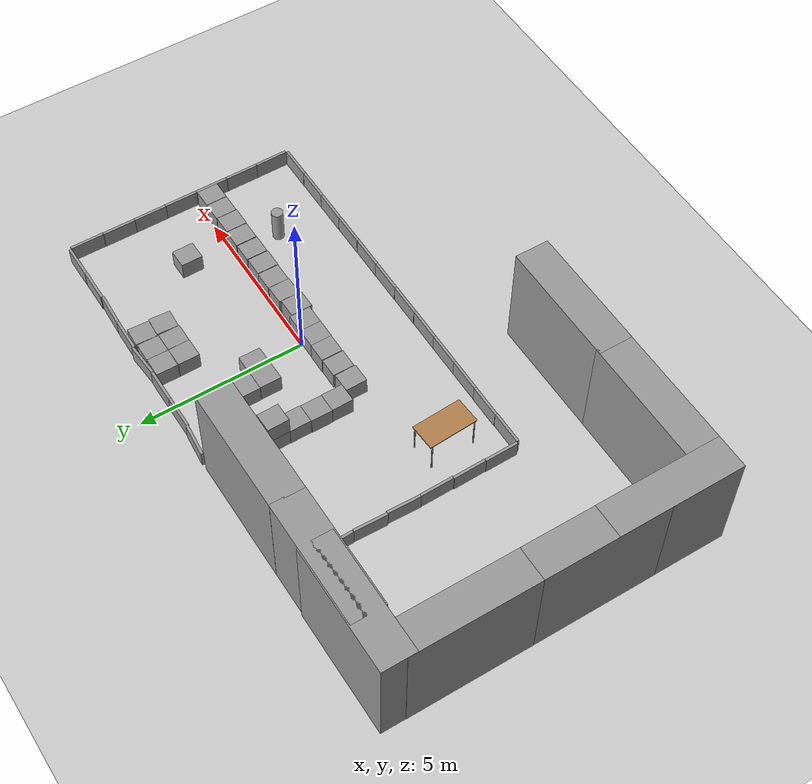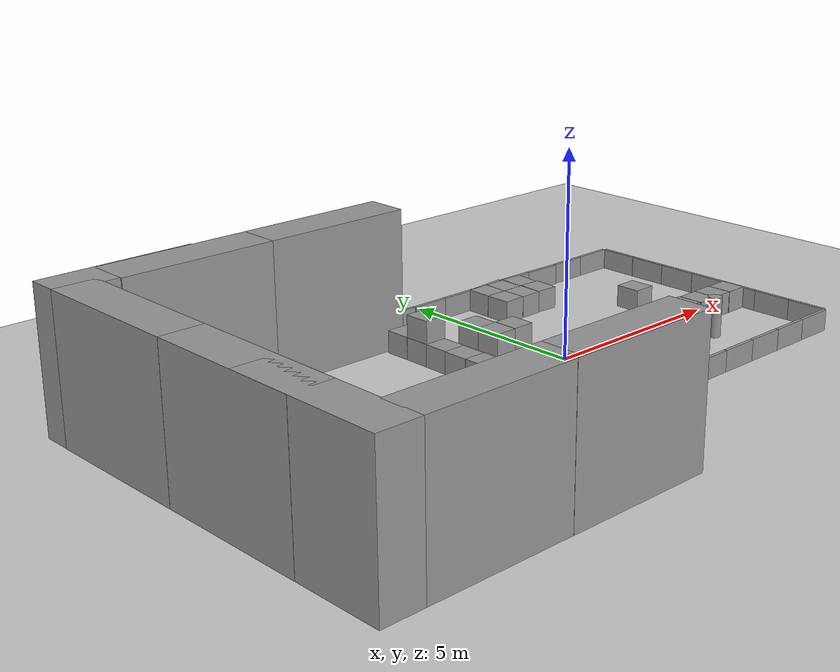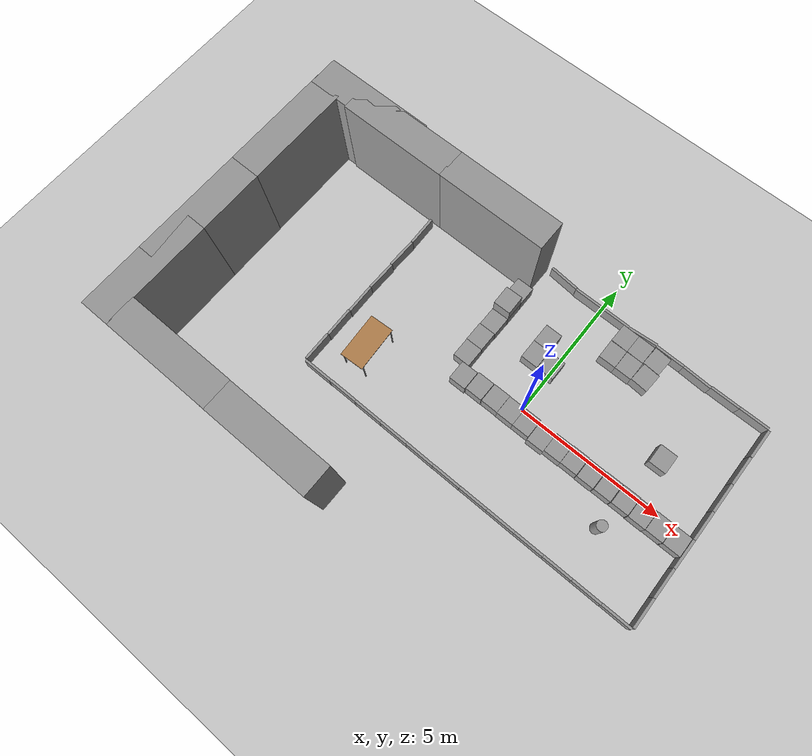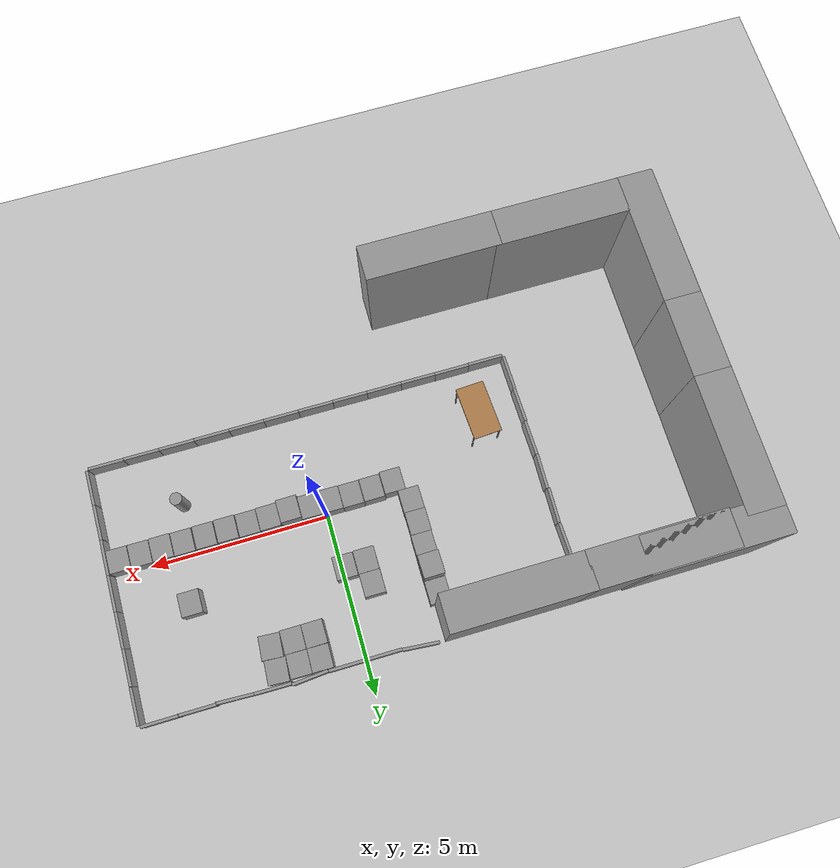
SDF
<sdf version="1.6">
 <world name="default">
  <light name="sun" type="directional">
   <pose>0 0 10 0 -0 0</pose>
   <diffuse>0.8 0.8 0.8 1</diffuse>
   <specular>0.2 0.2 0.2 1</specular>
   <attenuation>
    <range>1000</range>
    <constant>0.9</constant>
    <linear>0.01</linear>
    <quadratic>0.001</quadratic>
   </attenuation>
   <direction>-0.5 0.1 -0.9</direction>
  </light>
  <model name="ground_plane">
   <static>1</static>
   <link name="link">
    <collision name="collision">
     <geometry><plane><normal>0 0 1</normal><size>100 100</size></plane></geometry>
     <surface>
      <contact><collide_bitmask>65535</collide_bitmask></contact>
      <friction><ode><mu>100</mu><mu2>50</mu2></ode></friction>
     </surface>
    </collision>
    <visual name="visual">
     <cast_shadows>0</cast_shadows>
     <geometry><plane><normal>0 0 1</normal><size>100 100</size></plane></geometry>
     <material>
      <script><uri>file://media/materials/scripts/gazebo.material</uri><name>Gazebo/Grey</name></script>
     </material>
    </visual>
   </link>
  </model>
  <gravity>0 0 -9.8</gravity>
  <magnetic_field>6e-06 2.3e-05 -4.2e-05</magnetic_field>
  <atmosphere type="adiabatic"/>
  <physics name="default_physics" default="0" type="ode">
   <max_step_size>0.001</max_step_size>
   <real_time_factor>1</real_time_factor>
   <real_time_update_rate>1000</real_time_update_rate>
  </physics>
  <scene><ambient>0.4 0.4 0.4 1</ambient><background>0.7 0.7 0.7 1</background><shadows>1</shadows></scene>
  <audio><device>default</device></audio>
  <spherical_coordinates>
   <surface_model>EARTH_WGS84</surface_model>
   <latitude_deg>0</latitude_deg>
   <longitude_deg>0</longitude_deg>
   <elevation>0</elevation>
   <heading_deg>0</heading_deg>
  </spherical_coordinates>
  <model name="panel_0">
   <link name="link">
    <inertial>
     <mass>0.0428479</mass>
     <inertia>
      <ixx>0.00456249</ixx>
      <ixy>0</ixy>
      <ixz>0</ixz>
      <iyy>0.00101543</iyy>
      <iyz>0</iyz>
      <izz>0.00359426</izz>
     </inertia>
    </inertial>
    <pose>-0.996065 -0.479892 0.260289 0 -0 0</pose>
    <visual name="visual">
     <geometry><box><size>0.081299 1 0.527041</size></box></geometry>
     <material>
      <script><name>Gazebo/Grey</name><uri>file://media/materials/scripts/gazebo.material</uri></script>
      <emissive>0 0 0 1</emissive>
      <shader type="vertex"><normal_map>__default__</normal_map></shader>
      <ambient>0.3 0.3 0.3 1</ambient>
      <diffuse>0.7 0.7 0.7 1</diffuse>
      <specular>0.01 0.01 0.01 1</specular>
     </material>
    </visual>
    <collision name="collision">
     <geometry><box><size>0.081299 1 0.527041</size></box></geometry>
     <surface>
      <friction>
       <ode><mu>1</mu><mu2>1</mu2><fdir1>0 0 0</fdir1><slip1>0</slip1><slip2>0</slip2></ode>
       <torsional>
        <coefficient>1</coefficient>
        <patch_radius>0</patch_radius>
        <surface_radius>0</surface_radius>
        <use_patch_radius>1</use_patch_radius>
        <ode><slip>0</slip></ode>
       </torsional>
      </friction>
      <bounce><restitution_coefficient>0</restitution_coefficient><threshold>1e+06</threshold></bounce>
      <contact>
       <collide_without_contact>0</collide_without_contact>
       <collide_without_contact_bitmask>1</collide_without_contact_bitmask>
       <collide_bitmask>1</collide_bitmask>
       <ode>
        <soft_cfm>0</soft_cfm>
        <soft_erp>0.2</soft_erp>
        <kp>1e+13</kp>
        <kd>1</kd>
        <max_vel>0.01</max_vel>
        <min_depth>0</min_depth>
       </ode>
       <bullet>
        <split_impulse>1</split_impulse>
        <split_impulse_penetration_threshold>-0.01</split_impulse_penetration_threshold>
        <soft_cfm>0</soft_cfm>
        <soft_erp>0.2</soft_erp>
        <kp>1e+13</kp>
        <kd>1</kd>
       </bullet>
      </contact>
     </surface>
    </collision>
   </link>
   <static>0</static>
   <allow_auto_disable>0</allow_auto_disable>
   <pose>-5.05418 -0.988597 0.003222 -1e-06 0 0.022855</pose>
  </model>
  <model name="panel">
   <link name="link">
    <inertial>
     <mass>0.0428479</mass>
     <inertia>
      <ixx>0.00456249</ixx>
      <ixy>0</ixy>
      <ixz>0</ixz>
      <iyy>0.00101543</iyy>
      <iyz>0</iyz>
      <izz>0.00359426</izz>
     </inertia>
    </inertial>
    <pose>-0.996065 -0.479892 0.260289 0 -0 0</pose>
    <visual name="visual">
     <geometry><box><size>0.081299 1 0.527041</size></box></geometry>
     <material>
      <script><name>Gazebo/Grey</name><uri>file://media/materials/scripts/gazebo.material</uri></script>
      <emissive>0 0 0 1</emissive>
      <shader type="vertex"><normal_map>__default__</normal_map></shader>
      <ambient>0.3 0.3 0.3 1</ambient>
      <diffuse>0.7 0.7 0.7 1</diffuse>
      <specular>0.01 0.01 0.01 1</specular>
     </material>
    </visual>
    <collision name="collision">
     <geometry><box><size>0.081299 1 0.527041</size></box></geometry>
     <surface>
      <friction>
       <ode><mu>1</mu><mu2>1</mu2><fdir1>0 0 0</fdir1><slip1>0</slip1><slip2>0</slip2></ode>
       <torsional>
        <coefficient>1</coefficient>
        <patch_radius>0</patch_radius>
        <surface_radius>0</surface_radius>
        <use_patch_radius>1</use_patch_radius>
        <ode><slip>0</slip></ode>
       </torsional>
      </friction>
      <bounce><restitution_coefficient>0</restitution_coefficient><threshold>1e+06</threshold></bounce>
      <contact>
       <collide_without_contact>0</collide_without_contact>
       <collide_without_contact_bitmask>1</collide_without_contact_bitmask>
       <collide_bitmask>1</collide_bitmask>
       <ode>
        <soft_cfm>0</soft_cfm>
        <soft_erp>0.2</soft_erp>
        <kp>1e+13</kp>
        <kd>1</kd>
        <max_vel>0.01</max_vel>
        <min_depth>0</min_depth>
       </ode>
       <bullet>
        <split_impulse>1</split_impulse>
        <split_impulse_penetration_threshold>-0.01</split_impulse_penetration_threshold>
        <soft_cfm>0</soft_cfm>
        <soft_erp>0.2</soft_erp>
        <kp>1e+13</kp>
        <kd>1</kd>
       </bullet>
      </contact>
     </surface>
    </collision>
   </link>
   <static>0</static>
   <allow_auto_disable>0</allow_auto_disable>
   <pose>-5.04883 0.006609 0.003227 -4e-06 -0 0.017153</pose>
  </model>
  <model name="panel_1">
   <link name="link">
    <inertial>
     <mass>0.0428479</mass>
     <inertia>
      <ixx>0.00456249</ixx>
      <ixy>0</ixy>
      <ixz>0</ixz>
      <iyy>0.00101543</iyy>
      <iyz>0</iyz>
      <izz>0.00359426</izz>
     </inertia>
    </inertial>
    <pose>-0.996065 -0.479892 0.260289 0 -0 0</pose>
    <visual name="visual">
     <geometry><box><size>0.081299 1 0.527041</size></box></geometry>
     <material>
      <script><name>Gazebo/Grey</name><uri>file://media/materials/scripts/gazebo.material</uri></script>
      <emissive>0 0 0 1</emissive>
      <shader type="vertex"><normal_map>__default__</normal_map></shader>
      <ambient>0.3 0.3 0.3 1</ambient>
      <diffuse>0.7 0.7 0.7 1</diffuse>
      <specular>0.01 0.01 0.01 1</specular>
     </material>
    </visual>
    <collision name="collision">
     <geometry><box><size>0.081299 1 0.527041</size></box></geometry>
     <surface>
      <friction>
       <ode><mu>1</mu><mu2>1</mu2><fdir1>0 0 0</fdir1><slip1>0</slip1><slip2>0</slip2></ode>
       <torsional>
        <coefficient>1</coefficient>
        <patch_radius>0</patch_radius>
        <surface_radius>0</surface_radius>
        <use_patch_radius>1</use_patch_radius>
        <ode><slip>0</slip></ode>
       </torsional>
      </friction>
      <bounce><restitution_coefficient>0</restitution_coefficient><threshold>1e+06</threshold></bounce>
      <contact>
       <collide_without_contact>0</collide_without_contact>
       <collide_without_contact_bitmask>1</collide_without_contact_bitmask>
       <collide_bitmask>1</collide_bitmask>
       <ode>
        <soft_cfm>0</soft_cfm>
        <soft_erp>0.2</soft_erp>
        <kp>1e+13</kp>
        <kd>1</kd>
        <max_vel>0.01</max_vel>
        <min_depth>0</min_depth>
       </ode>
       <bullet>
        <split_impulse>1</split_impulse>
        <split_impulse_penetration_threshold>-0.01</split_impulse_penetration_threshold>
        <soft_cfm>0</soft_cfm>
        <soft_erp>0.2</soft_erp>
        <kp>1e+13</kp>
        <kd>1</kd>
       </bullet>
      </contact>
     </surface>
    </collision>
   </link>
   <static>0</static>
   <allow_auto_disable>0</allow_auto_disable>
   <pose>-5.02835 0.9633 0.003231 0 0 -0.027927</pose>
  </model>
  <model name="panel_2">
   <link name="link">
    <inertial>
     <mass>0.0428479</mass>
     <inertia>
      <ixx>0.00456249</ixx>
      <ixy>0</ixy>
      <ixz>0</ixz>
      <iyy>0.00101543</iyy>
      <iyz>0</iyz>
      <izz>0.00359426</izz>
     </inertia>
    </inertial>
    <pose>-0.996065 -0.479892 0.260289 0 -0 0</pose>
    <visual name="visual">
     <geometry><box><size>0.081299 1 0.527041</size></box></geometry>
     <material>
      <script><name>Gazebo/Grey</name><uri>file://media/materials/scripts/gazebo.material</uri></script>
      <emissive>0 0 0 1</emissive>
      <shader type="vertex"><normal_map>__default__</normal_map></shader>
      <ambient>0.3 0.3 0.3 1</ambient>
      <diffuse>0.7 0.7 0.7 1</diffuse>
      <specular>0.01 0.01 0.01 1</specular>
     </material>
    </visual>
    <collision name="collision">
     <geometry><box><size>0.081299 1 0.527041</size></box></geometry>
     <surface>
      <friction>
       <ode><mu>1</mu><mu2>1</mu2><fdir1>0 0 0</fdir1><slip1>0</slip1><slip2>0</slip2></ode>
       <torsional>
        <coefficient>1</coefficient>
        <patch_radius>0</patch_radius>
        <surface_radius>0</surface_radius>
        <use_patch_radius>1</use_patch_radius>
        <ode><slip>0</slip></ode>
       </torsional>
      </friction>
      <bounce><restitution_coefficient>0</restitution_coefficient><threshold>1e+06</threshold></bounce>
      <contact>
       <collide_without_contact>0</collide_without_contact>
       <collide_without_contact_bitmask>1</collide_without_contact_bitmask>
       <collide_bitmask>1</collide_bitmask>
       <ode>
        <soft_cfm>0</soft_cfm>
        <soft_erp>0.2</soft_erp>
        <kp>1e+13</kp>
        <kd>1</kd>
        <max_vel>0.01</max_vel>
        <min_depth>0</min_depth>
       </ode>
       <bullet>
        <split_impulse>1</split_impulse>
        <split_impulse_penetration_threshold>-0.01</split_impulse_penetration_threshold>
        <soft_cfm>0</soft_cfm>
        <soft_erp>0.2</soft_erp>
        <kp>1e+13</kp>
        <kd>1</kd>
       </bullet>
      </contact>
     </surface>
    </collision>
   </link>
   <static>0</static>
   <allow_auto_disable>0</allow_auto_disable>
   <pose>-5.0306 1.96587 0.003233 0 -1e-06 -0.029752</pose>
  </model>
  <model name="panel_3">
   <link name="link">
    <inertial>
     <mass>0.0428479</mass>
     <inertia>
      <ixx>0.00456249</ixx>
      <ixy>0</ixy>
      <ixz>0</ixz>
      <iyy>0.00101543</iyy>
      <iyz>0</iyz>
      <izz>0.00359426</izz>
     </inertia>
    </inertial>
    <pose>-0.996065 -0.479892 0.260289 0 -0 0</pose>
    <visual name="visual">
     <geometry><box><size>0.081299 1 0.527041</size></box></geometry>
     <material>
      <script><name>Gazebo/Grey</name><uri>file://media/materials/scripts/gazebo.material</uri></script>
      <emissive>0 0 0 1</emissive>
      <shader type="vertex"><normal_map>__default__</normal_map></shader>
      <ambient>0.3 0.3 0.3 1</ambient>
      <diffuse>0.7 0.7 0.7 1</diffuse>
      <specular>0.01 0.01 0.01 1</specular>
     </material>
    </visual>
    <collision name="collision">
     <geometry><box><size>0.081299 1 0.527041</size></box></geometry>
     <surface>
      <friction>
       <ode><mu>1</mu><mu2>1</mu2><fdir1>0 0 0</fdir1><slip1>0</slip1><slip2>0</slip2></ode>
       <torsional>
        <coefficient>1</coefficient>
        <patch_radius>0</patch_radius>
        <surface_radius>0</surface_radius>
        <use_patch_radius>1</use_patch_radius>
        <ode><slip>0</slip></ode>
       </torsional>
      </friction>
      <bounce><restitution_coefficient>0</restitution_coefficient><threshold>1e+06</threshold></bounce>
      <contact>
       <collide_without_contact>0</collide_without_contact>
       <collide_without_contact_bitmask>1</collide_without_contact_bitmask>
       <collide_bitmask>1</collide_bitmask>
       <ode>
        <soft_cfm>0</soft_cfm>
        <soft_erp>0.2</soft_erp>
        <kp>1e+13</kp>
        <kd>1</kd>
        <max_vel>0.01</max_vel>
        <min_depth>0</min_depth>
       </ode>
       <bullet>
        <split_impulse>1</split_impulse>
        <split_impulse_penetration_threshold>-0.01</split_impulse_penetration_threshold>
        <soft_cfm>0</soft_cfm>
        <soft_erp>0.2</soft_erp>
        <kp>1e+13</kp>
        <kd>1</kd>
       </bullet>
      </contact>
     </surface>
    </collision>
   </link>
   <static>0</static>
   <allow_auto_disable>0</allow_auto_disable>
   <pose>-5.0627 3.03614 0.003232 0 -0 0.026347</pose>
  </model>
  <model name="panel_4">
   <link name="link">
    <inertial>
     <mass>0.0428479</mass>
     <inertia>
      <ixx>0.00456249</ixx>
      <ixy>0</ixy>
      <ixz>0</ixz>
      <iyy>0.00101543</iyy>
      <iyz>0</iyz>
      <izz>0.00359426</izz>
     </inertia>
    </inertial>
    <pose>-0.996065 -0.479892 0.260289 0 -0 0</pose>
    <visual name="visual">
     <geometry><box><size>0.081299 1 0.527041</size></box></geometry>
     <material>
      <script><name>Gazebo/Grey</name><uri>file://media/materials/scripts/gazebo.material</uri></script>
      <emissive>0 0 0 1</emissive>
      <shader type="vertex"><normal_map>__default__</normal_map></shader>
      <ambient>0.3 0.3 0.3 1</ambient>
      <diffuse>0.7 0.7 0.7 1</diffuse>
      <specular>0.01 0.01 0.01 1</specular>
     </material>
    </visual>
    <collision name="collision">
     <geometry><box><size>0.081299 1 0.527041</size></box></geometry>
     <surface>
      <friction>
       <ode><mu>1</mu><mu2>1</mu2><fdir1>0 0 0</fdir1><slip1>0</slip1><slip2>0</slip2></ode>
       <torsional>
        <coefficient>1</coefficient>
        <patch_radius>0</patch_radius>
        <surface_radius>0</surface_radius>
        <use_patch_radius>1</use_patch_radius>
        <ode><slip>0</slip></ode>
       </torsional>
      </friction>
      <bounce><restitution_coefficient>0</restitution_coefficient><threshold>1e+06</threshold></bounce>
      <contact>
       <collide_without_contact>0</collide_without_contact>
       <collide_without_contact_bitmask>1</collide_without_contact_bitmask>
       <collide_bitmask>1</collide_bitmask>
       <ode>
        <soft_cfm>0</soft_cfm>
        <soft_erp>0.2</soft_erp>
        <kp>1e+13</kp>
        <kd>1</kd>
        <max_vel>0.01</max_vel>
        <min_depth>0</min_depth>
       </ode>
       <bullet>
        <split_impulse>1</split_impulse>
        <split_impulse_penetration_threshold>-0.01</split_impulse_penetration_threshold>
        <soft_cfm>0</soft_cfm>
        <soft_erp>0.2</soft_erp>
        <kp>1e+13</kp>
        <kd>1</kd>
       </bullet>
      </contact>
     </surface>
    </collision>
   </link>
   <static>0</static>
   <allow_auto_disable>0</allow_auto_disable>
   <pose>-5.04525 -1.99765 0.003231 4e-06 0 0.014171</pose>
  </model>
  <model name="panel_5">
   <link name="link">
    <inertial>
     <mass>0.0428479</mass>
     <inertia>
      <ixx>0.00456249</ixx>
      <ixy>0</ixy>
      <ixz>0</ixz>
      <iyy>0.00101543</iyy>
      <iyz>0</iyz>
      <izz>0.00359426</izz>
     </inertia>
    </inertial>
    <pose>-0.996065 -0.479892 0.260289 0 -0 0</pose>
    <visual name="visual">
     <geometry><box><size>0.081299 1 0.527041</size></box></geometry>
     <material>
      <script><name>Gazebo/Grey</name><uri>file://media/materials/scripts/gazebo.material</uri></script>
      <emissive>0 0 0 1</emissive>
      <shader type="vertex"><normal_map>__default__</normal_map></shader>
      <ambient>0.3 0.3 0.3 1</ambient>
      <diffuse>0.7 0.7 0.7 1</diffuse>
      <specular>0.01 0.01 0.01 1</specular>
     </material>
    </visual>
    <collision name="collision">
     <geometry><box><size>0.081299 1 0.527041</size></box></geometry>
     <surface>
      <friction>
       <ode><mu>1</mu><mu2>1</mu2><fdir1>0 0 0</fdir1><slip1>0</slip1><slip2>0</slip2></ode>
       <torsional>
        <coefficient>1</coefficient>
        <patch_radius>0</patch_radius>
        <surface_radius>0</surface_radius>
        <use_patch_radius>1</use_patch_radius>
        <ode><slip>0</slip></ode>
       </torsional>
      </friction>
      <bounce><restitution_coefficient>0</restitution_coefficient><threshold>1e+06</threshold></bounce>
      <contact>
       <collide_without_contact>0</collide_without_contact>
       <collide_without_contact_bitmask>1</collide_without_contact_bitmask>
       <collide_bitmask>1</collide_bitmask>
       <ode>
        <soft_cfm>0</soft_cfm>
        <soft_erp>0.2</soft_erp>
        <kp>1e+13</kp>
        <kd>1</kd>
        <max_vel>0.01</max_vel>
        <min_depth>0</min_depth>
       </ode>
       <bullet>
        <split_impulse>1</split_impulse>
        <split_impulse_penetration_threshold>-0.01</split_impulse_penetration_threshold>
        <soft_cfm>0</soft_cfm>
        <soft_erp>0.2</soft_erp>
        <kp>1e+13</kp>
        <kd>1</kd>
       </bullet>
      </contact>
     </surface>
    </collision>
   </link>
   <static>0</static>
   <allow_auto_disable>0</allow_auto_disable>
   <pose>7.04088 -0.024231 0.003231 1e-06 0 -0.004194</pose>
  </model>
  <model name="panel_6">
   <link name="link">
    <inertial>
     <mass>0.0428479</mass>
     <inertia>
      <ixx>0.00456249</ixx>
      <ixy>0</ixy>
      <ixz>0</ixz>
      <iyy>0.00101543</iyy>
      <iyz>0</iyz>
      <izz>0.00359426</izz>
     </inertia>
    </inertial>
    <pose>-0.996065 -0.479892 0.260289 0 -0 0</pose>
    <visual name="visual">
     <geometry><box><size>0.081299 1 0.527041</size></box></geometry>
     <material>
      <script><name>Gazebo/Grey</name><uri>file://media/materials/scripts/gazebo.material</uri></script>
      <emissive>0 0 0 1</emissive>
      <shader type="vertex"><normal_map>__default__</normal_map></shader>
      <ambient>0.3 0.3 0.3 1</ambient>
      <diffuse>0.7 0.7 0.7 1</diffuse>
      <specular>0.01 0.01 0.01 1</specular>
     </material>
    </visual>
    <collision name="collision">
     <geometry><box><size>0.081299 1 0.527041</size></box></geometry>
     <surface>
      <friction>
       <ode><mu>1</mu><mu2>1</mu2><fdir1>0 0 0</fdir1><slip1>0</slip1><slip2>0</slip2></ode>
       <torsional>
        <coefficient>1</coefficient>
        <patch_radius>0</patch_radius>
        <surface_radius>0</surface_radius>
        <use_patch_radius>1</use_patch_radius>
        <ode><slip>0</slip></ode>
       </torsional>
      </friction>
      <bounce><restitution_coefficient>0</restitution_coefficient><threshold>1e+06</threshold></bounce>
      <contact>
       <collide_without_contact>0</collide_without_contact>
       <collide_without_contact_bitmask>1</collide_without_contact_bitmask>
       <collide_bitmask>1</collide_bitmask>
       <ode>
        <soft_cfm>0</soft_cfm>
        <soft_erp>0.2</soft_erp>
        <kp>1e+13</kp>
        <kd>1</kd>
        <max_vel>0.01</max_vel>
        <min_depth>0</min_depth>
       </ode>
       <bullet>
        <split_impulse>1</split_impulse>
        <split_impulse_penetration_threshold>-0.01</split_impulse_penetration_threshold>
        <soft_cfm>0</soft_cfm>
        <soft_erp>0.2</soft_erp>
        <kp>1e+13</kp>
        <kd>1</kd>
       </bullet>
      </contact>
     </surface>
    </collision>
   </link>
   <static>0</static>
   <allow_auto_disable>0</allow_auto_disable>
   <pose>7.04227 0.98064 0.003225 -6e-06 -0 0.000389</pose>
  </model>
  <model name="panel_7">
   <link name="link">
    <inertial>
     <mass>0.0428479</mass>
     <inertia>
      <ixx>0.00456249</ixx>
      <ixy>0</ixy>
      <ixz>0</ixz>
      <iyy>0.00101543</iyy>
      <iyz>0</iyz>
      <izz>0.00359426</izz>
     </inertia>
    </inertial>
    <pose>-0.996065 -0.479892 0.260289 0 -0 0</pose>
    <visual name="visual">
     <geometry><box><size>0.081299 1 0.527041</size></box></geometry>
     <material>
      <script><name>Gazebo/Grey</name><uri>file://media/materials/scripts/gazebo.material</uri></script>
      <emissive>0 0 0 1</emissive>
      <shader type="vertex"><normal_map>__default__</normal_map></shader>
      <ambient>0.3 0.3 0.3 1</ambient>
      <diffuse>0.7 0.7 0.7 1</diffuse>
      <specular>0.01 0.01 0.01 1</specular>
     </material>
    </visual>
    <collision name="collision">
     <geometry><box><size>0.081299 1 0.527041</size></box></geometry>
     <surface>
      <friction>
       <ode><mu>1</mu><mu2>1</mu2><fdir1>0 0 0</fdir1><slip1>0</slip1><slip2>0</slip2></ode>
       <torsional>
        <coefficient>1</coefficient>
        <patch_radius>0</patch_radius>
        <surface_radius>0</surface_radius>
        <use_patch_radius>1</use_patch_radius>
        <ode><slip>0</slip></ode>
       </torsional>
      </friction>
      <bounce><restitution_coefficient>0</restitution_coefficient><threshold>1e+06</threshold></bounce>
      <contact>
       <collide_without_contact>0</collide_without_contact>
       <collide_without_contact_bitmask>1</collide_without_contact_bitmask>
       <collide_bitmask>1</collide_bitmask>
       <ode>
        <soft_cfm>0</soft_cfm>
        <soft_erp>0.2</soft_erp>
        <kp>1e+13</kp>
        <kd>1</kd>
        <max_vel>0.01</max_vel>
        <min_depth>0</min_depth>
       </ode>
       <bullet>
        <split_impulse>1</split_impulse>
        <split_impulse_penetration_threshold>-0.01</split_impulse_penetration_threshold>
        <soft_cfm>0</soft_cfm>
        <soft_erp>0.2</soft_erp>
        <kp>1e+13</kp>
        <kd>1</kd>
       </bullet>
      </contact>
     </surface>
    </collision>
   </link>
   <static>0</static>
   <allow_auto_disable>0</allow_auto_disable>
   <pose>7.03946 1.98026 0.003231 1e-06 -0 -7.8e-05</pose>
  </model>
  <model name="panel_8">
   <link name="link">
    <inertial>
     <mass>0.0428479</mass>
     <inertia>
      <ixx>0.00456249</ixx>
      <ixy>0</ixy>
      <ixz>0</ixz>
      <iyy>0.00101543</iyy>
      <iyz>0</iyz>
      <izz>0.00359426</izz>
     </inertia>
    </inertial>
    <pose>-0.996065 -0.479892 0.260289 0 -0 0</pose>
    <visual name="visual">
     <geometry><box><size>0.081299 1 0.527041</size></box></geometry>
     <material>
      <script><name>Gazebo/Grey</name><uri>file://media/materials/scripts/gazebo.material</uri></script>
      <emissive>0 0 0 1</emissive>
      <shader type="vertex"><normal_map>__default__</normal_map></shader>
      <ambient>0.3 0.3 0.3 1</ambient>
      <diffuse>0.7 0.7 0.7 1</diffuse>
      <specular>0.01 0.01 0.01 1</specular>
     </material>
    </visual>
    <collision name="collision">
     <geometry><box><size>0.081299 1 0.527041</size></box></geometry>
     <surface>
      <friction>
       <ode><mu>1</mu><mu2>1</mu2><fdir1>0 0 0</fdir1><slip1>0</slip1><slip2>0</slip2></ode>
       <torsional>
        <coefficient>1</coefficient>
        <patch_radius>0</patch_radius>
        <surface_radius>0</surface_radius>
        <use_patch_radius>1</use_patch_radius>
        <ode><slip>0</slip></ode>
       </torsional>
      </friction>
      <bounce><restitution_coefficient>0</restitution_coefficient><threshold>1e+06</threshold></bounce>
      <contact>
       <collide_without_contact>0</collide_without_contact>
       <collide_without_contact_bitmask>1</collide_without_contact_bitmask>
       <collide_bitmask>1</collide_bitmask>
       <ode>
        <soft_cfm>0</soft_cfm>
        <soft_erp>0.2</soft_erp>
        <kp>1e+13</kp>
        <kd>1</kd>
        <max_vel>0.01</max_vel>
        <min_depth>0</min_depth>
       </ode>
       <bullet>
        <split_impulse>1</split_impulse>
        <split_impulse_penetration_threshold>-0.01</split_impulse_penetration_threshold>
        <soft_cfm>0</soft_cfm>
        <soft_erp>0.2</soft_erp>
        <kp>1e+13</kp>
        <kd>1</kd>
       </bullet>
      </contact>
     </surface>
    </collision>
   </link>
   <static>0</static>
   <allow_auto_disable>0</allow_auto_disable>
   <pose>7.03923 2.97769 0.003227 -4e-06 -0 -0.002794</pose>
  </model>
  <model name="panel_9">
   <link name="link">
    <inertial>
     <mass>0.0428479</mass>
     <inertia>
      <ixx>0.00456249</ixx>
      <ixy>0</ixy>
      <ixz>0</ixz>
      <iyy>0.00101543</iyy>
      <iyz>0</iyz>
      <izz>0.00359426</izz>
     </inertia>
    </inertial>
    <pose>-0.996065 -0.479892 0.260289 0 -0 0</pose>
    <visual name="visual">
     <geometry><box><size>0.081299 1 0.527041</size></box></geometry>
     <material>
      <script><name>Gazebo/Grey</name><uri>file://media/materials/scripts/gazebo.material</uri></script>
      <emissive>0 0 0 1</emissive>
      <shader type="vertex"><normal_map>__default__</normal_map></shader>
      <ambient>0.3 0.3 0.3 1</ambient>
      <diffuse>0.7 0.7 0.7 1</diffuse>
      <specular>0.01 0.01 0.01 1</specular>
     </material>
    </visual>
    <collision name="collision">
     <geometry><box><size>0.081299 1 0.527041</size></box></geometry>
     <surface>
      <friction>
       <ode><mu>1</mu><mu2>1</mu2><fdir1>0 0 0</fdir1><slip1>0</slip1><slip2>0</slip2></ode>
       <torsional>
        <coefficient>1</coefficient>
        <patch_radius>0</patch_radius>
        <surface_radius>0</surface_radius>
        <use_patch_radius>1</use_patch_radius>
        <ode><slip>0</slip></ode>
       </torsional>
      </friction>
      <bounce><restitution_coefficient>0</restitution_coefficient><threshold>1e+06</threshold></bounce>
      <contact>
       <collide_without_contact>0</collide_without_contact>
       <collide_without_contact_bitmask>1</collide_without_contact_bitmask>
       <collide_bitmask>1</collide_bitmask>
       <ode>
        <soft_cfm>0</soft_cfm>
        <soft_erp>0.2</soft_erp>
        <kp>1e+13</kp>
        <kd>1</kd>
        <max_vel>0.01</max_vel>
        <min_depth>0</min_depth>
       </ode>
       <bullet>
        <split_impulse>1</split_impulse>
        <split_impulse_penetration_threshold>-0.01</split_impulse_penetration_threshold>
        <soft_cfm>0</soft_cfm>
        <soft_erp>0.2</soft_erp>
        <kp>1e+13</kp>
        <kd>1</kd>
       </bullet>
      </contact>
     </surface>
    </collision>
   </link>
   <static>0</static>
   <allow_auto_disable>0</allow_auto_disable>
   <pose>7.03497 -1.01885 0.00323 -1e-06 0 0.002619</pose>
  </model>
  <model name="panel_10">
   <link name="link">
    <inertial>
     <mass>0.0428479</mass>
     <inertia>
      <ixx>0.00456249</ixx>
      <ixy>0</ixy>
      <ixz>0</ixz>
      <iyy>0.00101543</iyy>
      <iyz>0</iyz>
      <izz>0.00359426</izz>
     </inertia>
    </inertial>
    <pose>-0.996065 -0.479892 0.260289 0 -0 0</pose>
    <visual name="visual">
     <geometry><box><size>0.081299 1 0.527041</size></box></geometry>
     <material>
      <script><name>Gazebo/Grey</name><uri>file://media/materials/scripts/gazebo.material</uri></script>
      <emissive>0 0 0 1</emissive>
      <shader type="vertex"><normal_map>__default__</normal_map></shader>
      <ambient>0.3 0.3 0.3 1</ambient>
      <diffuse>0.7 0.7 0.7 1</diffuse>
      <specular>0.01 0.01 0.01 1</specular>
     </material>
    </visual>
    <collision name="collision">
     <geometry><box><size>0.081299 1 0.527041</size></box></geometry>
     <surface>
      <friction>
       <ode><mu>1</mu><mu2>1</mu2><fdir1>0 0 0</fdir1><slip1>0</slip1><slip2>0</slip2></ode>
       <torsional>
        <coefficient>1</coefficient>
        <patch_radius>0</patch_radius>
        <surface_radius>0</surface_radius>
        <use_patch_radius>1</use_patch_radius>
        <ode><slip>0</slip></ode>
       </torsional>
      </friction>
      <bounce><restitution_coefficient>0</restitution_coefficient><threshold>1e+06</threshold></bounce>
      <contact>
       <collide_without_contact>0</collide_without_contact>
       <collide_without_contact_bitmask>1</collide_without_contact_bitmask>
       <collide_bitmask>1</collide_bitmask>
       <ode>
        <soft_cfm>0</soft_cfm>
        <soft_erp>0.2</soft_erp>
        <kp>1e+13</kp>
        <kd>1</kd>
        <max_vel>0.01</max_vel>
        <min_depth>0</min_depth>
       </ode>
       <bullet>
        <split_impulse>1</split_impulse>
        <split_impulse_penetration_threshold>-0.01</split_impulse_penetration_threshold>
        <soft_cfm>0</soft_cfm>
        <soft_erp>0.2</soft_erp>
        <kp>1e+13</kp>
        <kd>1</kd>
       </bullet>
      </contact>
     </surface>
    </collision>
   </link>
   <static>0</static>
   <allow_auto_disable>0</allow_auto_disable>
   <pose>7.03911 -2.01685 0.00323 -1e-06 -0 0.004812</pose>
  </model>
  <model name="panel_11">
   <link name="link">
    <inertial>
     <mass>0.0428479</mass>
     <inertia>
      <ixx>0.00456249</ixx>
      <ixy>0</ixy>
      <ixz>0</ixz>
      <iyy>0.00101543</iyy>
      <iyz>0</iyz>
      <izz>0.00359426</izz>
     </inertia>
    </inertial>
    <pose>-0.996065 -0.479892 0.260289 0 -0 0</pose>
    <visual name="visual">
     <geometry><box><size>0.081299 1 0.527041</size></box></geometry>
     <material>
      <script><name>Gazebo/Grey</name><uri>file://media/materials/scripts/gazebo.material</uri></script>
      <emissive>0 0 0 1</emissive>
      <shader type="vertex"><normal_map>__default__</normal_map></shader>
      <ambient>0.3 0.3 0.3 1</ambient>
      <diffuse>0.7 0.7 0.7 1</diffuse>
      <specular>0.01 0.01 0.01 1</specular>
     </material>
    </visual>
    <collision name="collision">
     <geometry><box><size>0.081299 1 0.527041</size></box></geometry>
     <surface>
      <friction>
       <ode><mu>1</mu><mu2>1</mu2><fdir1>0 0 0</fdir1><slip1>0</slip1><slip2>0</slip2></ode>
       <torsional>
        <coefficient>1</coefficient>
        <patch_radius>0</patch_radius>
        <surface_radius>0</surface_radius>
        <use_patch_radius>1</use_patch_radius>
        <ode><slip>0</slip></ode>
       </torsional>
      </friction>
      <bounce><restitution_coefficient>0</restitution_coefficient><threshold>1e+06</threshold></bounce>
      <contact>
       <collide_without_contact>0</collide_without_contact>
       <collide_without_contact_bitmask>1</collide_without_contact_bitmask>
       <collide_bitmask>1</collide_bitmask>
       <ode>
        <soft_cfm>0</soft_cfm>
        <soft_erp>0.2</soft_erp>
        <kp>1e+13</kp>
        <kd>1</kd>
        <max_vel>0.01</max_vel>
        <min_depth>0</min_depth>
       </ode>
       <bullet>
        <split_impulse>1</split_impulse>
        <split_impulse_penetration_threshold>-0.01</split_impulse_penetration_threshold>
        <soft_cfm>0</soft_cfm>
        <soft_erp>0.2</soft_erp>
        <kp>1e+13</kp>
        <kd>1</kd>
       </bullet>
      </contact>
     </surface>
    </collision>
   </link>
   <static>0</static>
   <allow_auto_disable>0</allow_auto_disable>
   <pose>-4.97363 -2.03274 0.003222 -1e-05 -0 1.5692</pose>
  </model>
  <model name="panel_12">
   <link name="link">
    <inertial>
     <mass>0.0428479</mass>
     <inertia>
      <ixx>0.00456249</ixx>
      <ixy>0</ixy>
      <ixz>0</ixz>
      <iyy>0.00101543</iyy>
      <iyz>0</iyz>
      <izz>0.00359426</izz>
     </inertia>
    </inertial>
    <pose>-0.996065 -0.479892 0.260289 0 -0 0</pose>
    <visual name="visual">
     <geometry><box><size>0.081299 1 0.527041</size></box></geometry>
     <material>
      <script><name>Gazebo/Grey</name><uri>file://media/materials/scripts/gazebo.material</uri></script>
      <emissive>0 0 0 1</emissive>
      <shader type="vertex"><normal_map>__default__</normal_map></shader>
      <ambient>0.3 0.3 0.3 1</ambient>
      <diffuse>0.7 0.7 0.7 1</diffuse>
      <specular>0.01 0.01 0.01 1</specular>
     </material>
    </visual>
    <collision name="collision">
     <geometry><box><size>0.081299 1 0.527041</size></box></geometry>
     <surface>
      <friction>
       <ode><mu>1</mu><mu2>1</mu2><fdir1>0 0 0</fdir1><slip1>0</slip1><slip2>0</slip2></ode>
       <torsional>
        <coefficient>1</coefficient>
        <patch_radius>0</patch_radius>
        <surface_radius>0</surface_radius>
        <use_patch_radius>1</use_patch_radius>
        <ode><slip>0</slip></ode>
       </torsional>
      </friction>
      <bounce><restitution_coefficient>0</restitution_coefficient><threshold>1e+06</threshold></bounce>
      <contact>
       <collide_without_contact>0</collide_without_contact>
       <collide_without_contact_bitmask>1</collide_without_contact_bitmask>
       <collide_bitmask>1</collide_bitmask>
       <ode>
        <soft_cfm>0</soft_cfm>
        <soft_erp>0.2</soft_erp>
        <kp>1e+13</kp>
        <kd>1</kd>
        <max_vel>0.01</max_vel>
        <min_depth>0</min_depth>
       </ode>
       <bullet>
        <split_impulse>1</split_impulse>
        <split_impulse_penetration_threshold>-0.01</split_impulse_penetration_threshold>
        <soft_cfm>0</soft_cfm>
        <soft_erp>0.2</soft_erp>
        <kp>1e+13</kp>
        <kd>1</kd>
       </bullet>
      </contact>
     </surface>
    </collision>
   </link>
   <static>0</static>
   <allow_auto_disable>0</allow_auto_disable>
   <pose>-5.97519 -2.04045 0.003232 0 -1e-06 1.56998</pose>
  </model>
  <model name="panel_13">
   <link name="link">
    <inertial>
     <mass>0.0428479</mass>
     <inertia>
      <ixx>0.00456249</ixx>
      <ixy>0</ixy>
      <ixz>0</ixz>
      <iyy>0.00101543</iyy>
      <iyz>0</iyz>
      <izz>0.00359426</izz>
     </inertia>
    </inertial>
    <pose>-0.996065 -0.479892 0.260289 0 -0 0</pose>
    <visual name="visual">
     <geometry><box><size>0.081299 1 0.527041</size></box></geometry>
     <material>
      <script><name>Gazebo/Grey</name><uri>file://media/materials/scripts/gazebo.material</uri></script>
      <emissive>0 0 0 1</emissive>
      <shader type="vertex"><normal_map>__default__</normal_map></shader>
      <ambient>0.3 0.3 0.3 1</ambient>
      <diffuse>0.7 0.7 0.7 1</diffuse>
      <specular>0.01 0.01 0.01 1</specular>
     </material>
    </visual>
    <collision name="collision">
     <geometry><box><size>0.081299 1 0.527041</size></box></geometry>
     <surface>
      <friction>
       <ode><mu>1</mu><mu2>1</mu2><fdir1>0 0 0</fdir1><slip1>0</slip1><slip2>0</slip2></ode>
       <torsional>
        <coefficient>1</coefficient>
        <patch_radius>0</patch_radius>
        <surface_radius>0</surface_radius>
        <use_patch_radius>1</use_patch_radius>
        <ode><slip>0</slip></ode>
       </torsional>
      </friction>
      <bounce><restitution_coefficient>0</restitution_coefficient><threshold>1e+06</threshold></bounce>
      <contact>
       <collide_without_contact>0</collide_without_contact>
       <collide_without_contact_bitmask>1</collide_without_contact_bitmask>
       <collide_bitmask>1</collide_bitmask>
       <ode>
        <soft_cfm>0</soft_cfm>
        <soft_erp>0.2</soft_erp>
        <kp>1e+13</kp>
        <kd>1</kd>
        <max_vel>0.01</max_vel>
        <min_depth>0</min_depth>
       </ode>
       <bullet>
        <split_impulse>1</split_impulse>
        <split_impulse_penetration_threshold>-0.01</split_impulse_penetration_threshold>
        <soft_cfm>0</soft_cfm>
        <soft_erp>0.2</soft_erp>
        <kp>1e+13</kp>
        <kd>1</kd>
       </bullet>
      </contact>
     </surface>
    </collision>
   </link>
   <static>0</static>
   <allow_auto_disable>0</allow_auto_disable>
   <pose>5.03022 5.04748 0.003232 1e-06 -0 1.57241</pose>
  </model>
  <model name="panel_14">
   <link name="link">
    <inertial>
     <mass>0.0428479</mass>
     <inertia>
      <ixx>0.00456249</ixx>
      <ixy>0</ixy>
      <ixz>0</ixz>
      <iyy>0.00101543</iyy>
      <iyz>0</iyz>
      <izz>0.00359426</izz>
     </inertia>
    </inertial>
    <pose>-0.996065 -0.479892 0.260289 0 -0 0</pose>
    <visual name="visual">
     <geometry><box><size>0.081299 1 0.527041</size></box></geometry>
     <material>
      <script><name>Gazebo/Grey</name><uri>file://media/materials/scripts/gazebo.material</uri></script>
      <emissive>0 0 0 1</emissive>
      <shader type="vertex"><normal_map>__default__</normal_map></shader>
      <ambient>0.3 0.3 0.3 1</ambient>
      <diffuse>0.7 0.7 0.7 1</diffuse>
      <specular>0.01 0.01 0.01 1</specular>
     </material>
    </visual>
    <collision name="collision">
     <geometry><box><size>0.081299 1 0.527041</size></box></geometry>
     <surface>
      <friction>
       <ode><mu>1</mu><mu2>1</mu2><fdir1>0 0 0</fdir1><slip1>0</slip1><slip2>0</slip2></ode>
       <torsional>
        <coefficient>1</coefficient>
        <patch_radius>0</patch_radius>
        <surface_radius>0</surface_radius>
        <use_patch_radius>1</use_patch_radius>
        <ode><slip>0</slip></ode>
       </torsional>
      </friction>
      <bounce><restitution_coefficient>0</restitution_coefficient><threshold>1e+06</threshold></bounce>
      <contact>
       <collide_without_contact>0</collide_without_contact>
       <collide_without_contact_bitmask>1</collide_without_contact_bitmask>
       <collide_bitmask>1</collide_bitmask>
       <ode>
        <soft_cfm>0</soft_cfm>
        <soft_erp>0.2</soft_erp>
        <kp>1e+13</kp>
        <kd>1</kd>
        <max_vel>0.01</max_vel>
        <min_depth>0</min_depth>
       </ode>
       <bullet>
        <split_impulse>1</split_impulse>
        <split_impulse_penetration_threshold>-0.01</split_impulse_penetration_threshold>
        <soft_cfm>0</soft_cfm>
        <soft_erp>0.2</soft_erp>
        <kp>1e+13</kp>
        <kd>1</kd>
       </bullet>
      </contact>
     </surface>
    </collision>
   </link>
   <static>0</static>
   <allow_auto_disable>0</allow_auto_disable>
   <pose>4.98668 3.05059 0.003222 -1e-05 -1e-06 -1.5755</pose>
  </model>
  <model name="panel_14_clone">
   <link name="link">
    <inertial>
     <mass>0.0428479</mass>
     <inertia>
      <ixx>0.00456249</ixx>
      <ixy>0</ixy>
      <ixz>0</ixz>
      <iyy>0.00101543</iyy>
      <iyz>0</iyz>
      <izz>0.00359426</izz>
     </inertia>
    </inertial>
    <pose>-0.996065 -0.479892 0.260289 0 -0 0</pose>
    <visual name="visual">
     <geometry><box><size>0.081299 1 0.527041</size></box></geometry>
     <material>
      <script><name>Gazebo/Grey</name><uri>file://media/materials/scripts/gazebo.material</uri></script>
      <emissive>0 0 0 1</emissive>
      <shader type="vertex"><normal_map>__default__</normal_map></shader>
      <ambient>0.3 0.3 0.3 1</ambient>
      <diffuse>0.7 0.7 0.7 1</diffuse>
      <specular>0.01 0.01 0.01 1</specular>
     </material>
    </visual>
    <collision name="collision">
     <geometry><box><size>0.081299 1 0.527041</size></box></geometry>
     <surface>
      <friction>
       <ode><mu>1</mu><mu2>1</mu2><fdir1>0 0 0</fdir1><slip1>0</slip1><slip2>0</slip2></ode>
       <torsional>
        <coefficient>1</coefficient>
        <patch_radius>0</patch_radius>
        <surface_radius>0</surface_radius>
        <use_patch_radius>1</use_patch_radius>
        <ode><slip>0</slip></ode>
       </torsional>
      </friction>
      <bounce><restitution_coefficient>0</restitution_coefficient><threshold>1e+06</threshold></bounce>
      <contact>
       <collide_without_contact>0</collide_without_contact>
       <collide_without_contact_bitmask>1</collide_without_contact_bitmask>
       <collide_bitmask>1</collide_bitmask>
       <ode>
        <soft_cfm>0</soft_cfm>
        <soft_erp>0.2</soft_erp>
        <kp>1e+13</kp>
        <kd>1</kd>
        <max_vel>0.01</max_vel>
        <min_depth>0</min_depth>
       </ode>
       <bullet>
        <split_impulse>1</split_impulse>
        <split_impulse_penetration_threshold>-0.01</split_impulse_penetration_threshold>
        <soft_cfm>0</soft_cfm>
        <soft_erp>0.2</soft_erp>
        <kp>1e+13</kp>
        <kd>1</kd>
       </bullet>
      </contact>
     </surface>
    </collision>
   </link>
   <static>0</static>
   <allow_auto_disable>0</allow_auto_disable>
   <pose>3.94843 3.03214 0.003228 -4e-06 -0 -1.61229</pose>
  </model>
  <model name="panel_14_clone_0">
   <link name="link">
    <inertial>
     <mass>0.0428479</mass>
     <inertia>
      <ixx>0.00456249</ixx>
      <ixy>0</ixy>
      <ixz>0</ixz>
      <iyy>0.00101543</iyy>
      <iyz>0</iyz>
      <izz>0.00359426</izz>
     </inertia>
    </inertial>
    <pose>-0.996065 -0.479892 0.260289 0 -0 0</pose>
    <visual name="visual">
     <geometry><box><size>0.081299 1 0.527041</size></box></geometry>
     <material>
      <script><name>Gazebo/Grey</name><uri>file://media/materials/scripts/gazebo.material</uri></script>
      <emissive>0 0 0 1</emissive>
      <shader type="vertex"><normal_map>__default__</normal_map></shader>
      <ambient>0.3 0.3 0.3 1</ambient>
      <diffuse>0.7 0.7 0.7 1</diffuse>
      <specular>0.01 0.01 0.01 1</specular>
     </material>
    </visual>
    <collision name="collision">
     <geometry><box><size>0.081299 1 0.527041</size></box></geometry>
     <surface>
      <friction>
       <ode><mu>1</mu><mu2>1</mu2><fdir1>0 0 0</fdir1><slip1>0</slip1><slip2>0</slip2></ode>
       <torsional>
        <coefficient>1</coefficient>
        <patch_radius>0</patch_radius>
        <surface_radius>0</surface_radius>
        <use_patch_radius>1</use_patch_radius>
        <ode><slip>0</slip></ode>
       </torsional>
      </friction>
      <bounce><restitution_coefficient>0</restitution_coefficient><threshold>1e+06</threshold></bounce>
      <contact>
       <collide_without_contact>0</collide_without_contact>
       <collide_without_contact_bitmask>1</collide_without_contact_bitmask>
       <collide_bitmask>1</collide_bitmask>
       <ode>
        <soft_cfm>0</soft_cfm>
        <soft_erp>0.2</soft_erp>
        <kp>1e+13</kp>
        <kd>1</kd>
        <max_vel>0.01</max_vel>
        <min_depth>0</min_depth>
       </ode>
       <bullet>
        <split_impulse>1</split_impulse>
        <split_impulse_penetration_threshold>-0.01</split_impulse_penetration_threshold>
        <soft_cfm>0</soft_cfm>
        <soft_erp>0.2</soft_erp>
        <kp>1e+13</kp>
        <kd>1</kd>
       </bullet>
      </contact>
     </surface>
    </collision>
   </link>
   <static>0</static>
   <allow_auto_disable>0</allow_auto_disable>
   <pose>2.9755 3.0735 0.003228 -4e-06 0 -1.58488</pose>
  </model>
  <model name="panel_14_clone_1">
   <link name="link">
    <inertial>
     <mass>0.0428479</mass>
     <inertia>
      <ixx>0.00456249</ixx>
      <ixy>0</ixy>
      <ixz>0</ixz>
      <iyy>0.00101543</iyy>
      <iyz>0</iyz>
      <izz>0.00359426</izz>
     </inertia>
    </inertial>
    <pose>-0.996065 -0.479892 0.260289 0 -0 0</pose>
    <visual name="visual">
     <geometry><box><size>0.081299 1 0.527041</size></box></geometry>
     <material>
      <script><name>Gazebo/Grey</name><uri>file://media/materials/scripts/gazebo.material</uri></script>
      <emissive>0 0 0 1</emissive>
      <shader type="vertex"><normal_map>__default__</normal_map></shader>
      <ambient>0.3 0.3 0.3 1</ambient>
      <diffuse>0.7 0.7 0.7 1</diffuse>
      <specular>0.01 0.01 0.01 1</specular>
     </material>
    </visual>
    <collision name="collision">
     <geometry><box><size>0.081299 1 0.527041</size></box></geometry>
     <surface>
      <friction>
       <ode><mu>1</mu><mu2>1</mu2><fdir1>0 0 0</fdir1><slip1>0</slip1><slip2>0</slip2></ode>
       <torsional>
        <coefficient>1</coefficient>
        <patch_radius>0</patch_radius>
        <surface_radius>0</surface_radius>
        <use_patch_radius>1</use_patch_radius>
        <ode><slip>0</slip></ode>
       </torsional>
      </friction>
      <bounce><restitution_coefficient>0</restitution_coefficient><threshold>1e+06</threshold></bounce>
      <contact>
       <collide_without_contact>0</collide_without_contact>
       <collide_without_contact_bitmask>1</collide_without_contact_bitmask>
       <collide_bitmask>1</collide_bitmask>
       <ode>
        <soft_cfm>0</soft_cfm>
        <soft_erp>0.2</soft_erp>
        <kp>1e+13</kp>
        <kd>1</kd>
        <max_vel>0.01</max_vel>
        <min_depth>0</min_depth>
       </ode>
       <bullet>
        <split_impulse>1</split_impulse>
        <split_impulse_penetration_threshold>-0.01</split_impulse_penetration_threshold>
        <soft_cfm>0</soft_cfm>
        <soft_erp>0.2</soft_erp>
        <kp>1e+13</kp>
        <kd>1</kd>
       </bullet>
      </contact>
     </surface>
    </collision>
   </link>
   <static>0</static>
   <allow_auto_disable>0</allow_auto_disable>
   <pose>2.06663 3.12643 0.003231 8e-06 -0 -1.49013</pose>
  </model>
  <model name="panel_14_clone_2">
   <link name="link">
    <inertial>
     <mass>0.0428479</mass>
     <inertia>
      <ixx>0.00456249</ixx>
      <ixy>0</ixy>
      <ixz>0</ixz>
      <iyy>0.00101543</iyy>
      <iyz>0</iyz>
      <izz>0.00359426</izz>
     </inertia>
    </inertial>
    <pose>-0.996065 -0.479892 0.260289 0 -0 0</pose>
    <visual name="visual">
     <geometry><box><size>0.081299 1 0.527041</size></box></geometry>
     <material>
      <script><name>Gazebo/Grey</name><uri>file://media/materials/scripts/gazebo.material</uri></script>
      <emissive>0 0 0 1</emissive>
      <shader type="vertex"><normal_map>__default__</normal_map></shader>
      <ambient>0.3 0.3 0.3 1</ambient>
      <diffuse>0.7 0.7 0.7 1</diffuse>
      <specular>0.01 0.01 0.01 1</specular>
     </material>
    </visual>
    <collision name="collision">
     <geometry><box><size>0.081299 1 0.527041</size></box></geometry>
     <surface>
      <friction>
       <ode><mu>1</mu><mu2>1</mu2><fdir1>0 0 0</fdir1><slip1>0</slip1><slip2>0</slip2></ode>
       <torsional>
        <coefficient>1</coefficient>
        <patch_radius>0</patch_radius>
        <surface_radius>0</surface_radius>
        <use_patch_radius>1</use_patch_radius>
        <ode><slip>0</slip></ode>
       </torsional>
      </friction>
      <bounce><restitution_coefficient>0</restitution_coefficient><threshold>1e+06</threshold></bounce>
      <contact>
       <collide_without_contact>0</collide_without_contact>
       <collide_without_contact_bitmask>1</collide_without_contact_bitmask>
       <collide_bitmask>1</collide_bitmask>
       <ode>
        <soft_cfm>0</soft_cfm>
        <soft_erp>0.2</soft_erp>
        <kp>1e+13</kp>
        <kd>1</kd>
        <max_vel>0.01</max_vel>
        <min_depth>0</min_depth>
       </ode>
       <bullet>
        <split_impulse>1</split_impulse>
        <split_impulse_penetration_threshold>-0.01</split_impulse_penetration_threshold>
        <soft_cfm>0</soft_cfm>
        <soft_erp>0.2</soft_erp>
        <kp>1e+13</kp>
        <kd>1</kd>
       </bullet>
      </contact>
     </surface>
    </collision>
   </link>
   <static>0</static>
   <allow_auto_disable>0</allow_auto_disable>
   <pose>0.979904 3.05667 0.00323 -1e-06 -0 -1.57204</pose>
  </model>
  <model name="panel_14_clone_3">
   <link name="link">
    <inertial>
     <mass>0.0428479</mass>
     <inertia>
      <ixx>0.00456249</ixx>
      <ixy>0</ixy>
      <ixz>0</ixz>
      <iyy>0.00101543</iyy>
      <iyz>0</iyz>
      <izz>0.00359426</izz>
     </inertia>
    </inertial>
    <pose>-0.996065 -0.479892 0.260289 0 -0 0</pose>
    <visual name="visual">
     <geometry><box><size>0.081299 1 0.527041</size></box></geometry>
     <material>
      <script><name>Gazebo/Grey</name><uri>file://media/materials/scripts/gazebo.material</uri></script>
      <emissive>0 0 0 1</emissive>
      <shader type="vertex"><normal_map>__default__</normal_map></shader>
      <ambient>0.3 0.3 0.3 1</ambient>
      <diffuse>0.7 0.7 0.7 1</diffuse>
      <specular>0.01 0.01 0.01 1</specular>
     </material>
    </visual>
    <collision name="collision">
     <geometry><box><size>0.081299 1 0.527041</size></box></geometry>
     <surface>
      <friction>
       <ode><mu>1</mu><mu2>1</mu2><fdir1>0 0 0</fdir1><slip1>0</slip1><slip2>0</slip2></ode>
       <torsional>
        <coefficient>1</coefficient>
        <patch_radius>0</patch_radius>
        <surface_radius>0</surface_radius>
        <use_patch_radius>1</use_patch_radius>
        <ode><slip>0</slip></ode>
       </torsional>
      </friction>
      <bounce><restitution_coefficient>0</restitution_coefficient><threshold>1e+06</threshold></bounce>
      <contact>
       <collide_without_contact>0</collide_without_contact>
       <collide_without_contact_bitmask>1</collide_without_contact_bitmask>
       <collide_bitmask>1</collide_bitmask>
       <ode>
        <soft_cfm>0</soft_cfm>
        <soft_erp>0.2</soft_erp>
        <kp>1e+13</kp>
        <kd>1</kd>
        <max_vel>0.01</max_vel>
        <min_depth>0</min_depth>
       </ode>
       <bullet>
        <split_impulse>1</split_impulse>
        <split_impulse_penetration_threshold>-0.01</split_impulse_penetration_threshold>
        <soft_cfm>0</soft_cfm>
        <soft_erp>0.2</soft_erp>
        <kp>1e+13</kp>
        <kd>1</kd>
       </bullet>
      </contact>
     </surface>
    </collision>
   </link>
   <static>0</static>
   <allow_auto_disable>0</allow_auto_disable>
   <pose>-0.019937 3.056 0.003231 6e-06 -0 -1.57183</pose>
  </model>
  <model name="panel_14_clone_4">
   <link name="link">
    <inertial>
     <mass>0.0428479</mass>
     <inertia>
      <ixx>0.00456249</ixx>
      <ixy>0</ixy>
      <ixz>0</ixz>
      <iyy>0.00101543</iyy>
      <iyz>0</iyz>
      <izz>0.00359426</izz>
     </inertia>
    </inertial>
    <pose>-0.996065 -0.479892 0.260289 0 -0 0</pose>
    <visual name="visual">
     <geometry><box><size>0.081299 1 0.527041</size></box></geometry>
     <material>
      <script><name>Gazebo/Grey</name><uri>file://media/materials/scripts/gazebo.material</uri></script>
      <emissive>0 0 0 1</emissive>
      <shader type="vertex"><normal_map>__default__</normal_map></shader>
      <ambient>0.3 0.3 0.3 1</ambient>
      <diffuse>0.7 0.7 0.7 1</diffuse>
      <specular>0.01 0.01 0.01 1</specular>
     </material>
    </visual>
    <collision name="collision">
     <geometry><box><size>0.081299 1 0.527041</size></box></geometry>
     <surface>
      <friction>
       <ode><mu>1</mu><mu2>1</mu2><fdir1>0 0 0</fdir1><slip1>0</slip1><slip2>0</slip2></ode>
       <torsional>
        <coefficient>1</coefficient>
        <patch_radius>0</patch_radius>
        <surface_radius>0</surface_radius>
        <use_patch_radius>1</use_patch_radius>
        <ode><slip>0</slip></ode>
       </torsional>
      </friction>
      <bounce><restitution_coefficient>0</restitution_coefficient><threshold>1e+06</threshold></bounce>
      <contact>
       <collide_without_contact>0</collide_without_contact>
       <collide_without_contact_bitmask>1</collide_without_contact_bitmask>
       <collide_bitmask>1</collide_bitmask>
       <ode>
        <soft_cfm>0</soft_cfm>
        <soft_erp>0.2</soft_erp>
        <kp>1e+13</kp>
        <kd>1</kd>
        <max_vel>0.01</max_vel>
        <min_depth>0</min_depth>
       </ode>
       <bullet>
        <split_impulse>1</split_impulse>
        <split_impulse_penetration_threshold>-0.01</split_impulse_penetration_threshold>
        <soft_cfm>0</soft_cfm>
        <soft_erp>0.2</soft_erp>
        <kp>1e+13</kp>
        <kd>1</kd>
       </bullet>
      </contact>
     </surface>
    </collision>
   </link>
   <static>0</static>
   <allow_auto_disable>0</allow_auto_disable>
   <pose>-1.10574 3.07917 0.003232 4e-06 -0 -1.65518</pose>
  </model>
  <model name="wall_4_1_3">
   <link name="link">
    <inertial>
     <mass>12.3337</mass>
     <inertia><ixx>12.5329</ixx><ixy>0</ixy><ixz>0</ixz><iyy>25.4731</iyy><iyz>0</iyz><izz>14.9958</izz></inertia>
    </inertial>
    <pose>-2.9941 -0.388092 1.21174 0 -0 0</pose>
    <visual name="visual">
     <geometry><box><size>3.68647 1 3.34571</size></box></geometry>
     <material>
      <script><name>Gazebo/Grey</name><uri>file://media/materials/scripts/gazebo.material</uri></script>
     </material>
    </visual>
    <collision name="collision">
     <geometry><box><size>3.68647 1 3.34571</size></box></geometry>
     <surface>
      <friction>
       <ode><mu>1</mu><mu2>1</mu2><fdir1>0 0 0</fdir1><slip1>0</slip1><slip2>0</slip2></ode>
       <torsional>
        <coefficient>1</coefficient>
        <patch_radius>0</patch_radius>
        <surface_radius>0</surface_radius>
        <use_patch_radius>1</use_patch_radius>
        <ode><slip>0</slip></ode>
       </torsional>
      </friction>
      <bounce><restitution_coefficient>0</restitution_coefficient><threshold>1e+06</threshold></bounce>
      <contact>
       <collide_without_contact>0</collide_without_contact>
       <collide_without_contact_bitmask>1</collide_without_contact_bitmask>
       <collide_bitmask>1</collide_bitmask>
       <ode>
        <soft_cfm>0</soft_cfm>
        <soft_erp>0.2</soft_erp>
        <kp>1e+13</kp>
        <kd>1</kd>
        <max_vel>0.01</max_vel>
        <min_depth>0</min_depth>
       </ode>
       <bullet>
        <split_impulse>1</split_impulse>
        <split_impulse_penetration_threshold>-0.01</split_impulse_penetration_threshold>
        <soft_cfm>0</soft_cfm>
        <soft_erp>0.2</soft_erp>
        <kp>1e+13</kp>
        <kd>1</kd>
       </bullet>
      </contact>
     </surface>
    </collision>
   </link>
   <static>1</static>
   <allow_auto_disable>0</allow_auto_disable>
   <pose>-1.01297 4.06271 0.5 0 -0 0</pose>
  </model>
  <model name="wall_4_1_3_clone">
   <link name="link">
    <inertial>
     <mass>12.3337</mass>
     <inertia><ixx>12.5329</ixx><ixy>0</ixy><ixz>0</ixz><iyy>25.4731</iyy><iyz>0</iyz><izz>14.9958</izz></inertia>
    </inertial>
    <pose>-2.9941 -0.388092 1.21174 0 -0 0</pose>
    <visual name="visual">
     <geometry><box><size>3.68647 1 3.34571</size></box></geometry>
     <material>
      <script><name>Gazebo/Grey</name><uri>file://media/materials/scripts/gazebo.material</uri></script>
     </material>
    </visual>
    <collision name="collision">
     <geometry><box><size>3.68647 1 3.34571</size></box></geometry>
     <surface>
      <friction>
       <ode><mu>1</mu><mu2>1</mu2><fdir1>0 0 0</fdir1><slip1>0</slip1><slip2>0</slip2></ode>
       <torsional>
        <coefficient>1</coefficient>
        <patch_radius>0</patch_radius>
        <surface_radius>0</surface_radius>
        <use_patch_radius>1</use_patch_radius>
        <ode><slip>0</slip></ode>
       </torsional>
      </friction>
      <bounce><restitution_coefficient>0</restitution_coefficient><threshold>1e+06</threshold></bounce>
      <contact>
       <collide_without_contact>0</collide_without_contact>
       <collide_without_contact_bitmask>1</collide_without_contact_bitmask>
       <collide_bitmask>1</collide_bitmask>
       <ode>
        <soft_cfm>0</soft_cfm>
        <soft_erp>0.2</soft_erp>
        <kp>1e+13</kp>
        <kd>1</kd>
        <max_vel>0.01</max_vel>
        <min_depth>0</min_depth>
       </ode>
       <bullet>
        <split_impulse>1</split_impulse>
        <split_impulse_penetration_threshold>-0.01</split_impulse_penetration_threshold>
        <soft_cfm>0</soft_cfm>
        <soft_erp>0.2</soft_erp>
        <kp>1e+13</kp>
        <kd>1</kd>
       </bullet>
      </contact>
     </surface>
    </collision>
   </link>
   <static>1</static>
   <allow_auto_disable>0</allow_auto_disable>
   <pose>-4.65872 4.06004 0.5 0 -0 0</pose>
  </model>
  <model name="wall_4_1_3_clone_0">
   <link name="link">
    <inertial>
     <mass>12.3337</mass>
     <inertia><ixx>12.5329</ixx><ixy>0</ixy><ixz>0</ixz><iyy>25.4731</iyy><iyz>0</iyz><izz>14.9958</izz></inertia>
    </inertial>
    <pose>-2.9941 -0.388092 1.21174 0 -0 0</pose>
    <visual name="visual">
     <geometry><box><size>3.68647 1 3.34571</size></box></geometry>
     <material>
      <script><name>Gazebo/Grey</name><uri>file://media/materials/scripts/gazebo.material</uri></script>
     </material>
    </visual>
    <collision name="collision">
     <geometry><box><size>3.68647 1 3.34571</size></box></geometry>
     <surface>
      <friction>
       <ode><mu>1</mu><mu2>1</mu2><fdir1>0 0 0</fdir1><slip1>0</slip1><slip2>0</slip2></ode>
       <torsional>
        <coefficient>1</coefficient>
        <patch_radius>0</patch_radius>
        <surface_radius>0</surface_radius>
        <use_patch_radius>1</use_patch_radius>
        <ode><slip>0</slip></ode>
       </torsional>
      </friction>
      <bounce><restitution_coefficient>0</restitution_coefficient><threshold>1e+06</threshold></bounce>
      <contact>
       <collide_without_contact>0</collide_without_contact>
       <collide_without_contact_bitmask>1</collide_without_contact_bitmask>
       <collide_bitmask>1</collide_bitmask>
       <ode>
        <soft_cfm>0</soft_cfm>
        <soft_erp>0.2</soft_erp>
        <kp>1e+13</kp>
        <kd>1</kd>
        <max_vel>0.01</max_vel>
        <min_depth>0</min_depth>
       </ode>
       <bullet>
        <split_impulse>1</split_impulse>
        <split_impulse_penetration_threshold>-0.01</split_impulse_penetration_threshold>
        <soft_cfm>0</soft_cfm>
        <soft_erp>0.2</soft_erp>
        <kp>1e+13</kp>
        <kd>1</kd>
       </bullet>
      </contact>
     </surface>
    </collision>
   </link>
   <static>1</static>
   <allow_auto_disable>0</allow_auto_disable>
   <pose>-5.05797 -5.12167 0.5 0 -0 0</pose>
  </model>
  <model name="wall_4_1_3_clone_1">
   <link name="link">
    <inertial>
     <mass>12.3337</mass>
     <inertia><ixx>12.5329</ixx><ixy>0</ixy><ixz>0</ixz><iyy>25.4731</iyy><iyz>0</iyz><izz>14.9958</izz></inertia>
    </inertial>
    <pose>-2.9941 -0.388092 1.21174 0 -0 0</pose>
    <visual name="visual">
     <geometry><box><size>3.68647 1 3.34571</size></box></geometry>
     <material>
      <script><name>Gazebo/Grey</name><uri>file://media/materials/scripts/gazebo.material</uri></script>
     </material>
    </visual>
    <collision name="collision">
     <geometry><box><size>3.68647 1 3.34571</size></box></geometry>
     <surface>
      <friction>
       <ode><mu>1</mu><mu2>1</mu2><fdir1>0 0 0</fdir1><slip1>0</slip1><slip2>0</slip2></ode>
       <torsional>
        <coefficient>1</coefficient>
        <patch_radius>0</patch_radius>
        <surface_radius>0</surface_radius>
        <use_patch_radius>1</use_patch_radius>
        <ode><slip>0</slip></ode>
       </torsional>
      </friction>
      <bounce><restitution_coefficient>0</restitution_coefficient><threshold>1e+06</threshold></bounce>
      <contact>
       <collide_without_contact>0</collide_without_contact>
       <collide_without_contact_bitmask>1</collide_without_contact_bitmask>
       <collide_bitmask>1</collide_bitmask>
       <ode>
        <soft_cfm>0</soft_cfm>
        <soft_erp>0.2</soft_erp>
        <kp>1e+13</kp>
        <kd>1</kd>
        <max_vel>0.01</max_vel>
        <min_depth>0</min_depth>
       </ode>
       <bullet>
        <split_impulse>1</split_impulse>
        <split_impulse_penetration_threshold>-0.01</split_impulse_penetration_threshold>
        <soft_cfm>0</soft_cfm>
        <soft_erp>0.2</soft_erp>
        <kp>1e+13</kp>
        <kd>1</kd>
       </bullet>
      </contact>
     </surface>
    </collision>
   </link>
   <static>1</static>
   <allow_auto_disable>0</allow_auto_disable>
   <pose>-1.52472 -5.12582 0.5 0 -0 0</pose>
  </model>
  <model name="wall_4_1_3_clone_2">
   <link name="link">
    <inertial>
     <mass>12.3337</mass>
     <inertia><ixx>12.5329</ixx><ixy>0</ixy><ixz>0</ixz><iyy>25.4731</iyy><iyz>0</iyz><izz>14.9958</izz></inertia>
    </inertial>
    <pose>-2.9941 -0.388092 1.21174 0 -0 0</pose>
    <visual name="visual">
     <geometry><box><size>3.68647 1 3.34571</size></box></geometry>
     <material>
      <script><name>Gazebo/Grey</name><uri>file://media/materials/scripts/gazebo.material</uri></script>
     </material>
    </visual>
    <collision name="collision">
     <geometry><box><size>3.68647 1 3.34571</size></box></geometry>
     <surface>
      <friction>
       <ode><mu>1</mu><mu2>1</mu2><fdir1>0 0 0</fdir1><slip1>0</slip1><slip2>0</slip2></ode>
       <torsional>
        <coefficient>1</coefficient>
        <patch_radius>0</patch_radius>
        <surface_radius>0</surface_radius>
        <use_patch_radius>1</use_patch_radius>
        <ode><slip>0</slip></ode>
       </torsional>
      </friction>
      <bounce><restitution_coefficient>0</restitution_coefficient><threshold>1e+06</threshold></bounce>
      <contact>
       <collide_without_contact>0</collide_without_contact>
       <collide_without_contact_bitmask>1</collide_without_contact_bitmask>
       <collide_bitmask>1</collide_bitmask>
       <ode>
        <soft_cfm>0</soft_cfm>
        <soft_erp>0.2</soft_erp>
        <kp>1e+13</kp>
        <kd>1</kd>
        <max_vel>0.01</max_vel>
        <min_depth>0</min_depth>
       </ode>
       <bullet>
        <split_impulse>1</split_impulse>
        <split_impulse_penetration_threshold>-0.01</split_impulse_penetration_threshold>
        <soft_cfm>0</soft_cfm>
        <soft_erp>0.2</soft_erp>
        <kp>1e+13</kp>
        <kd>1</kd>
       </bullet>
      </contact>
     </surface>
    </collision>
   </link>
   <static>1</static>
   <allow_auto_disable>0</allow_auto_disable>
   <pose>-10.7382 4.65294 0.5 0 -0 1.56894</pose>
  </model>
  <model name="wall_4_1_3_clone_2_clone">
   <link name="link">
    <inertial>
     <mass>12.3337</mass>
     <inertia><ixx>12.5329</ixx><ixy>0</ixy><ixz>0</ixz><iyy>25.4731</iyy><iyz>0</iyz><izz>14.9958</izz></inertia>
    </inertial>
    <pose>-2.9941 -0.388092 1.21174 0 -0 0</pose>
    <visual name="visual">
     <geometry><box><size>3.68647 1 3.34571</size></box></geometry>
     <material>
      <script><name>Gazebo/Grey</name><uri>file://media/materials/scripts/gazebo.material</uri></script>
     </material>
    </visual>
    <collision name="collision">
     <geometry><box><size>3.68647 1 3.34571</size></box></geometry>
     <surface>
      <friction>
       <ode><mu>1</mu><mu2>1</mu2><fdir1>0 0 0</fdir1><slip1>0</slip1><slip2>0</slip2></ode>
       <torsional>
        <coefficient>1</coefficient>
        <patch_radius>0</patch_radius>
        <surface_radius>0</surface_radius>
        <use_patch_radius>1</use_patch_radius>
        <ode><slip>0</slip></ode>
       </torsional>
      </friction>
      <bounce><restitution_coefficient>0</restitution_coefficient><threshold>1e+06</threshold></bounce>
      <contact>
       <collide_without_contact>0</collide_without_contact>
       <collide_without_contact_bitmask>1</collide_without_contact_bitmask>
       <collide_bitmask>1</collide_bitmask>
       <ode>
        <soft_cfm>0</soft_cfm>
        <soft_erp>0.2</soft_erp>
        <kp>1e+13</kp>
        <kd>1</kd>
        <max_vel>0.01</max_vel>
        <min_depth>0</min_depth>
       </ode>
       <bullet>
        <split_impulse>1</split_impulse>
        <split_impulse_penetration_threshold>-0.01</split_impulse_penetration_threshold>
        <soft_cfm>0</soft_cfm>
        <soft_erp>0.2</soft_erp>
        <kp>1e+13</kp>
        <kd>1</kd>
       </bullet>
      </contact>
     </surface>
    </collision>
   </link>
   <static>1</static>
   <allow_auto_disable>0</allow_auto_disable>
   <pose>-10.743 0.966495 0.5 0 -0 1.56894</pose>
  </model>
  <model name="wall_4_1_3_clone_2_clone_0">
   <link name="link">
    <inertial>
     <mass>12.3337</mass>
     <inertia><ixx>12.5329</ixx><ixy>0</ixy><ixz>0</ixz><iyy>25.4731</iyy><iyz>0</iyz><izz>14.9958</izz></inertia>
    </inertial>
    <pose>-2.9941 -0.388092 1.21174 0 -0 0</pose>
    <visual name="visual">
     <geometry><box><size>3.68647 1 3.34571</size></box></geometry>
     <material>
      <script><name>Gazebo/Grey</name><uri>file://media/materials/scripts/gazebo.material</uri></script>
     </material>
    </visual>
    <collision name="collision">
     <geometry><box><size>3.68647 1 3.34571</size></box></geometry>
     <surface>
      <friction>
       <ode><mu>1</mu><mu2>1</mu2><fdir1>0 0 0</fdir1><slip1>0</slip1><slip2>0</slip2></ode>
       <torsional>
        <coefficient>1</coefficient>
        <patch_radius>0</patch_radius>
        <surface_radius>0</surface_radius>
        <use_patch_radius>1</use_patch_radius>
        <ode><slip>0</slip></ode>
       </torsional>
      </friction>
      <bounce><restitution_coefficient>0</restitution_coefficient><threshold>1e+06</threshold></bounce>
      <contact>
       <collide_without_contact>0</collide_without_contact>
       <collide_without_contact_bitmask>1</collide_without_contact_bitmask>
       <collide_bitmask>1</collide_bitmask>
       <ode>
        <soft_cfm>0</soft_cfm>
        <soft_erp>0.2</soft_erp>
        <kp>1e+13</kp>
        <kd>1</kd>
        <max_vel>0.01</max_vel>
        <min_depth>0</min_depth>
       </ode>
       <bullet>
        <split_impulse>1</split_impulse>
        <split_impulse_penetration_threshold>-0.01</split_impulse_penetration_threshold>
        <soft_cfm>0</soft_cfm>
        <soft_erp>0.2</soft_erp>
        <kp>1e+13</kp>
        <kd>1</kd>
       </bullet>
      </contact>
     </surface>
    </collision>
   </link>
   <static>1</static>
   <allow_auto_disable>0</allow_auto_disable>
   <pose>-10.7437 -1.1722 0.5 0 -0 1.56894</pose>
  </model>
  <model name="panel_14_clone_1_clone">
   <link name="link">
    <inertial>
     <mass>0.0428479</mass>
     <inertia>
      <ixx>0.00456249</ixx>
      <ixy>0</ixy>
      <ixz>0</ixz>
      <iyy>0.00101543</iyy>
      <iyz>0</iyz>
      <izz>0.00359426</izz>
     </inertia>
    </inertial>
    <pose>-0.996065 -0.479892 0.260289 0 -0 0</pose>
    <visual name="visual">
     <geometry><box><size>0.081299 1 0.527041</size></box></geometry>
     <material>
      <script><name>Gazebo/Grey</name><uri>file://media/materials/scripts/gazebo.material</uri></script>
      <emissive>0 0 0 1</emissive>
      <shader type="vertex"><normal_map>__default__</normal_map></shader>
      <ambient>0.3 0.3 0.3 1</ambient>
      <diffuse>0.7 0.7 0.7 1</diffuse>
      <specular>0.01 0.01 0.01 1</specular>
     </material>
    </visual>
    <collision name="collision">
     <geometry><box><size>0.081299 1 0.527041</size></box></geometry>
     <surface>
      <friction>
       <ode><mu>1</mu><mu2>1</mu2><fdir1>0 0 0</fdir1><slip1>0</slip1><slip2>0</slip2></ode>
       <torsional>
        <coefficient>1</coefficient>
        <patch_radius>0</patch_radius>
        <surface_radius>0</surface_radius>
        <use_patch_radius>1</use_patch_radius>
        <ode><slip>0</slip></ode>
       </torsional>
      </friction>
      <bounce><restitution_coefficient>0</restitution_coefficient><threshold>1e+06</threshold></bounce>
      <contact>
       <collide_without_contact>0</collide_without_contact>
       <collide_without_contact_bitmask>1</collide_without_contact_bitmask>
       <collide_bitmask>1</collide_bitmask>
       <ode>
        <soft_cfm>0</soft_cfm>
        <soft_erp>0.2</soft_erp>
        <kp>1e+13</kp>
        <kd>1</kd>
        <max_vel>0.01</max_vel>
        <min_depth>0</min_depth>
       </ode>
       <bullet>
        <split_impulse>1</split_impulse>
        <split_impulse_penetration_threshold>-0.01</split_impulse_penetration_threshold>
        <soft_cfm>0</soft_cfm>
        <soft_erp>0.2</soft_erp>
        <kp>1e+13</kp>
        <kd>1</kd>
       </bullet>
      </contact>
     </surface>
    </collision>
   </link>
   <static>0</static>
   <allow_auto_disable>0</allow_auto_disable>
   <pose>5.98558 -4.03892 0.003223 -9e-06 0 -1.57313</pose>
  </model>
  <model name="panel_14_clone_1_clone_clone">
   <link name="link">
    <inertial>
     <mass>0.0428479</mass>
     <inertia>
      <ixx>0.00456249</ixx>
      <ixy>0</ixy>
      <ixz>0</ixz>
      <iyy>0.00101543</iyy>
      <iyz>0</iyz>
      <izz>0.00359426</izz>
     </inertia>
    </inertial>
    <pose>-0.996065 -0.479892 0.260289 0 -0 0</pose>
    <visual name="visual">
     <geometry><box><size>0.081299 1 0.527041</size></box></geometry>
     <material>
      <script><name>Gazebo/Grey</name><uri>file://media/materials/scripts/gazebo.material</uri></script>
      <emissive>0 0 0 1</emissive>
      <shader type="vertex"><normal_map>__default__</normal_map></shader>
      <ambient>0.3 0.3 0.3 1</ambient>
      <diffuse>0.7 0.7 0.7 1</diffuse>
      <specular>0.01 0.01 0.01 1</specular>
     </material>
    </visual>
    <collision name="collision">
     <geometry><box><size>0.081299 1 0.527041</size></box></geometry>
     <surface>
      <friction>
       <ode><mu>1</mu><mu2>1</mu2><fdir1>0 0 0</fdir1><slip1>0</slip1><slip2>0</slip2></ode>
       <torsional>
        <coefficient>1</coefficient>
        <patch_radius>0</patch_radius>
        <surface_radius>0</surface_radius>
        <use_patch_radius>1</use_patch_radius>
        <ode><slip>0</slip></ode>
       </torsional>
      </friction>
      <bounce><restitution_coefficient>0</restitution_coefficient><threshold>1e+06</threshold></bounce>
      <contact>
       <collide_without_contact>0</collide_without_contact>
       <collide_without_contact_bitmask>1</collide_without_contact_bitmask>
       <collide_bitmask>1</collide_bitmask>
       <ode>
        <soft_cfm>0</soft_cfm>
        <soft_erp>0.2</soft_erp>
        <kp>1e+13</kp>
        <kd>1</kd>
        <max_vel>0.01</max_vel>
        <min_depth>0</min_depth>
       </ode>
       <bullet>
        <split_impulse>1</split_impulse>
        <split_impulse_penetration_threshold>-0.01</split_impulse_penetration_threshold>
        <soft_cfm>0</soft_cfm>
        <soft_erp>0.2</soft_erp>
        <kp>1e+13</kp>
        <kd>1</kd>
       </bullet>
      </contact>
     </surface>
    </collision>
   </link>
   <static>0</static>
   <allow_auto_disable>0</allow_auto_disable>
   <pose>4.98482 -4.04279 0.003232 1e-06 -0 -1.57377</pose>
  </model>
  <model name="panel_14_clone_1_clone_clone_0">
   <link name="link">
    <inertial>
     <mass>0.0428479</mass>
     <inertia>
      <ixx>0.00456249</ixx>
      <ixy>0</ixy>
      <ixz>0</ixz>
      <iyy>0.00101543</iyy>
      <iyz>0</iyz>
      <izz>0.00359426</izz>
     </inertia>
    </inertial>
    <pose>-0.996065 -0.479892 0.260289 0 -0 0</pose>
    <visual name="visual">
     <geometry><box><size>0.081299 1 0.527041</size></box></geometry>
     <material>
      <script><name>Gazebo/Grey</name><uri>file://media/materials/scripts/gazebo.material</uri></script>
      <emissive>0 0 0 1</emissive>
      <shader type="vertex"><normal_map>__default__</normal_map></shader>
      <ambient>0.3 0.3 0.3 1</ambient>
      <diffuse>0.7 0.7 0.7 1</diffuse>
      <specular>0.01 0.01 0.01 1</specular>
     </material>
    </visual>
    <collision name="collision">
     <geometry><box><size>0.081299 1 0.527041</size></box></geometry>
     <surface>
      <friction>
       <ode><mu>1</mu><mu2>1</mu2><fdir1>0 0 0</fdir1><slip1>0</slip1><slip2>0</slip2></ode>
       <torsional>
        <coefficient>1</coefficient>
        <patch_radius>0</patch_radius>
        <surface_radius>0</surface_radius>
        <use_patch_radius>1</use_patch_radius>
        <ode><slip>0</slip></ode>
       </torsional>
      </friction>
      <bounce><restitution_coefficient>0</restitution_coefficient><threshold>1e+06</threshold></bounce>
      <contact>
       <collide_without_contact>0</collide_without_contact>
       <collide_without_contact_bitmask>1</collide_without_contact_bitmask>
       <collide_bitmask>1</collide_bitmask>
       <ode>
        <soft_cfm>0</soft_cfm>
        <soft_erp>0.2</soft_erp>
        <kp>1e+13</kp>
        <kd>1</kd>
        <max_vel>0.01</max_vel>
        <min_depth>0</min_depth>
       </ode>
       <bullet>
        <split_impulse>1</split_impulse>
        <split_impulse_penetration_threshold>-0.01</split_impulse_penetration_threshold>
        <soft_cfm>0</soft_cfm>
        <soft_erp>0.2</soft_erp>
        <kp>1e+13</kp>
        <kd>1</kd>
       </bullet>
      </contact>
     </surface>
    </collision>
   </link>
   <static>0</static>
   <allow_auto_disable>0</allow_auto_disable>
   <pose>3.98458 -4.04089 0.003225 -6e-06 -0 -1.574</pose>
  </model>
  <model name="panel_14_clone_1_clone_clone_1">
   <link name="link">
    <inertial>
     <mass>0.0428479</mass>
     <inertia>
      <ixx>0.00456249</ixx>
      <ixy>0</ixy>
      <ixz>0</ixz>
      <iyy>0.00101543</iyy>
      <iyz>0</iyz>
      <izz>0.00359426</izz>
     </inertia>
    </inertial>
    <pose>-0.996065 -0.479892 0.260289 0 -0 0</pose>
    <visual name="visual">
     <geometry><box><size>0.081299 1 0.527041</size></box></geometry>
     <material>
      <script><name>Gazebo/Grey</name><uri>file://media/materials/scripts/gazebo.material</uri></script>
      <emissive>0 0 0 1</emissive>
      <shader type="vertex"><normal_map>__default__</normal_map></shader>
      <ambient>0.3 0.3 0.3 1</ambient>
      <diffuse>0.7 0.7 0.7 1</diffuse>
      <specular>0.01 0.01 0.01 1</specular>
     </material>
    </visual>
    <collision name="collision">
     <geometry><box><size>0.081299 1 0.527041</size></box></geometry>
     <surface>
      <friction>
       <ode><mu>1</mu><mu2>1</mu2><fdir1>0 0 0</fdir1><slip1>0</slip1><slip2>0</slip2></ode>
       <torsional>
        <coefficient>1</coefficient>
        <patch_radius>0</patch_radius>
        <surface_radius>0</surface_radius>
        <use_patch_radius>1</use_patch_radius>
        <ode><slip>0</slip></ode>
       </torsional>
      </friction>
      <bounce><restitution_coefficient>0</restitution_coefficient><threshold>1e+06</threshold></bounce>
      <contact>
       <collide_without_contact>0</collide_without_contact>
       <collide_without_contact_bitmask>1</collide_without_contact_bitmask>
       <collide_bitmask>1</collide_bitmask>
       <ode>
        <soft_cfm>0</soft_cfm>
        <soft_erp>0.2</soft_erp>
        <kp>1e+13</kp>
        <kd>1</kd>
        <max_vel>0.01</max_vel>
        <min_depth>0</min_depth>
       </ode>
       <bullet>
        <split_impulse>1</split_impulse>
        <split_impulse_penetration_threshold>-0.01</split_impulse_penetration_threshold>
        <soft_cfm>0</soft_cfm>
        <soft_erp>0.2</soft_erp>
        <kp>1e+13</kp>
        <kd>1</kd>
       </bullet>
      </contact>
     </surface>
    </collision>
   </link>
   <static>0</static>
   <allow_auto_disable>0</allow_auto_disable>
   <pose>2.98661 -4.04181 0.003231 4e-06 -0 -1.57165</pose>
  </model>
  <model name="panel_14_clone_1_clone_clone_2">
   <link name="link">
    <inertial>
     <mass>0.0428479</mass>
     <inertia>
      <ixx>0.00456249</ixx>
      <ixy>0</ixy>
      <ixz>0</ixz>
      <iyy>0.00101543</iyy>
      <iyz>0</iyz>
      <izz>0.00359426</izz>
     </inertia>
    </inertial>
    <pose>-0.996065 -0.479892 0.260289 0 -0 0</pose>
    <visual name="visual">
     <geometry><box><size>0.081299 1 0.527041</size></box></geometry>
     <material>
      <script><name>Gazebo/Grey</name><uri>file://media/materials/scripts/gazebo.material</uri></script>
      <emissive>0 0 0 1</emissive>
      <shader type="vertex"><normal_map>__default__</normal_map></shader>
      <ambient>0.3 0.3 0.3 1</ambient>
      <diffuse>0.7 0.7 0.7 1</diffuse>
      <specular>0.01 0.01 0.01 1</specular>
     </material>
    </visual>
    <collision name="collision">
     <geometry><box><size>0.081299 1 0.527041</size></box></geometry>
     <surface>
      <friction>
       <ode><mu>1</mu><mu2>1</mu2><fdir1>0 0 0</fdir1><slip1>0</slip1><slip2>0</slip2></ode>
       <torsional>
        <coefficient>1</coefficient>
        <patch_radius>0</patch_radius>
        <surface_radius>0</surface_radius>
        <use_patch_radius>1</use_patch_radius>
        <ode><slip>0</slip></ode>
       </torsional>
      </friction>
      <bounce><restitution_coefficient>0</restitution_coefficient><threshold>1e+06</threshold></bounce>
      <contact>
       <collide_without_contact>0</collide_without_contact>
       <collide_without_contact_bitmask>1</collide_without_contact_bitmask>
       <collide_bitmask>1</collide_bitmask>
       <ode>
        <soft_cfm>0</soft_cfm>
        <soft_erp>0.2</soft_erp>
        <kp>1e+13</kp>
        <kd>1</kd>
        <max_vel>0.01</max_vel>
        <min_depth>0</min_depth>
       </ode>
       <bullet>
        <split_impulse>1</split_impulse>
        <split_impulse_penetration_threshold>-0.01</split_impulse_penetration_threshold>
        <soft_cfm>0</soft_cfm>
        <soft_erp>0.2</soft_erp>
        <kp>1e+13</kp>
        <kd>1</kd>
       </bullet>
      </contact>
     </surface>
    </collision>
   </link>
   <static>0</static>
   <allow_auto_disable>0</allow_auto_disable>
   <pose>1.98332 -4.04352 0.003231 1e-05 -0 -1.57459</pose>
  </model>
  <model name="panel_14_clone_1_clone_clone_3">
   <link name="link">
    <inertial>
     <mass>0.0428479</mass>
     <inertia>
      <ixx>0.00456249</ixx>
      <ixy>0</ixy>
      <ixz>0</ixz>
      <iyy>0.00101543</iyy>
      <iyz>0</iyz>
      <izz>0.00359426</izz>
     </inertia>
    </inertial>
    <pose>-0.996065 -0.479892 0.260289 0 -0 0</pose>
    <visual name="visual">
     <geometry><box><size>0.081299 1 0.527041</size></box></geometry>
     <material>
      <script><name>Gazebo/Grey</name><uri>file://media/materials/scripts/gazebo.material</uri></script>
      <emissive>0 0 0 1</emissive>
      <shader type="vertex"><normal_map>__default__</normal_map></shader>
      <ambient>0.3 0.3 0.3 1</ambient>
      <diffuse>0.7 0.7 0.7 1</diffuse>
      <specular>0.01 0.01 0.01 1</specular>
     </material>
    </visual>
    <collision name="collision">
     <geometry><box><size>0.081299 1 0.527041</size></box></geometry>
     <surface>
      <friction>
       <ode><mu>1</mu><mu2>1</mu2><fdir1>0 0 0</fdir1><slip1>0</slip1><slip2>0</slip2></ode>
       <torsional>
        <coefficient>1</coefficient>
        <patch_radius>0</patch_radius>
        <surface_radius>0</surface_radius>
        <use_patch_radius>1</use_patch_radius>
        <ode><slip>0</slip></ode>
       </torsional>
      </friction>
      <bounce><restitution_coefficient>0</restitution_coefficient><threshold>1e+06</threshold></bounce>
      <contact>
       <collide_without_contact>0</collide_without_contact>
       <collide_without_contact_bitmask>1</collide_without_contact_bitmask>
       <collide_bitmask>1</collide_bitmask>
       <ode>
        <soft_cfm>0</soft_cfm>
        <soft_erp>0.2</soft_erp>
        <kp>1e+13</kp>
        <kd>1</kd>
        <max_vel>0.01</max_vel>
        <min_depth>0</min_depth>
       </ode>
       <bullet>
        <split_impulse>1</split_impulse>
        <split_impulse_penetration_threshold>-0.01</split_impulse_penetration_threshold>
        <soft_cfm>0</soft_cfm>
        <soft_erp>0.2</soft_erp>
        <kp>1e+13</kp>
        <kd>1</kd>
       </bullet>
      </contact>
     </surface>
    </collision>
   </link>
   <static>0</static>
   <allow_auto_disable>0</allow_auto_disable>
   <pose>0.984938 -4.04067 0.003227 -4e-06 -0 -1.57273</pose>
  </model>
  <model name="panel_14_clone_1_clone_clone_4">
   <link name="link">
    <inertial>
     <mass>0.0428479</mass>
     <inertia>
      <ixx>0.00456249</ixx>
      <ixy>0</ixy>
      <ixz>0</ixz>
      <iyy>0.00101543</iyy>
      <iyz>0</iyz>
      <izz>0.00359426</izz>
     </inertia>
    </inertial>
    <pose>-0.996065 -0.479892 0.260289 0 -0 0</pose>
    <visual name="visual">
     <geometry><box><size>0.081299 1 0.527041</size></box></geometry>
     <material>
      <script><name>Gazebo/Grey</name><uri>file://media/materials/scripts/gazebo.material</uri></script>
      <emissive>0 0 0 1</emissive>
      <shader type="vertex"><normal_map>__default__</normal_map></shader>
      <ambient>0.3 0.3 0.3 1</ambient>
      <diffuse>0.7 0.7 0.7 1</diffuse>
      <specular>0.01 0.01 0.01 1</specular>
     </material>
    </visual>
    <collision name="collision">
     <geometry><box><size>0.081299 1 0.527041</size></box></geometry>
     <surface>
      <friction>
       <ode><mu>1</mu><mu2>1</mu2><fdir1>0 0 0</fdir1><slip1>0</slip1><slip2>0</slip2></ode>
       <torsional>
        <coefficient>1</coefficient>
        <patch_radius>0</patch_radius>
        <surface_radius>0</surface_radius>
        <use_patch_radius>1</use_patch_radius>
        <ode><slip>0</slip></ode>
       </torsional>
      </friction>
      <bounce><restitution_coefficient>0</restitution_coefficient><threshold>1e+06</threshold></bounce>
      <contact>
       <collide_without_contact>0</collide_without_contact>
       <collide_without_contact_bitmask>1</collide_without_contact_bitmask>
       <collide_bitmask>1</collide_bitmask>
       <ode>
        <soft_cfm>0</soft_cfm>
        <soft_erp>0.2</soft_erp>
        <kp>1e+13</kp>
        <kd>1</kd>
        <max_vel>0.01</max_vel>
        <min_depth>0</min_depth>
       </ode>
       <bullet>
        <split_impulse>1</split_impulse>
        <split_impulse_penetration_threshold>-0.01</split_impulse_penetration_threshold>
        <soft_cfm>0</soft_cfm>
        <soft_erp>0.2</soft_erp>
        <kp>1e+13</kp>
        <kd>1</kd>
       </bullet>
      </contact>
     </surface>
    </collision>
   </link>
   <static>0</static>
   <allow_auto_disable>0</allow_auto_disable>
   <pose>-0.017438 -4.04151 0.003231 1e-05 0 -1.57455</pose>
  </model>
  <model name="panel_14_clone_1_clone_clone_5">
   <link name="link">
    <inertial>
     <mass>0.0428479</mass>
     <inertia>
      <ixx>0.00456249</ixx>
      <ixy>0</ixy>
      <ixz>0</ixz>
      <iyy>0.00101543</iyy>
      <iyz>0</iyz>
      <izz>0.00359426</izz>
     </inertia>
    </inertial>
    <pose>-0.996065 -0.479892 0.260289 0 -0 0</pose>
    <visual name="visual">
     <geometry><box><size>0.081299 1 0.527041</size></box></geometry>
     <material>
      <script><name>Gazebo/Grey</name><uri>file://media/materials/scripts/gazebo.material</uri></script>
      <emissive>0 0 0 1</emissive>
      <shader type="vertex"><normal_map>__default__</normal_map></shader>
      <ambient>0.3 0.3 0.3 1</ambient>
      <diffuse>0.7 0.7 0.7 1</diffuse>
      <specular>0.01 0.01 0.01 1</specular>
     </material>
    </visual>
    <collision name="collision">
     <geometry><box><size>0.081299 1 0.527041</size></box></geometry>
     <surface>
      <friction>
       <ode><mu>1</mu><mu2>1</mu2><fdir1>0 0 0</fdir1><slip1>0</slip1><slip2>0</slip2></ode>
       <torsional>
        <coefficient>1</coefficient>
        <patch_radius>0</patch_radius>
        <surface_radius>0</surface_radius>
        <use_patch_radius>1</use_patch_radius>
        <ode><slip>0</slip></ode>
       </torsional>
      </friction>
      <bounce><restitution_coefficient>0</restitution_coefficient><threshold>1e+06</threshold></bounce>
      <contact>
       <collide_without_contact>0</collide_without_contact>
       <collide_without_contact_bitmask>1</collide_without_contact_bitmask>
       <collide_bitmask>1</collide_bitmask>
       <ode>
        <soft_cfm>0</soft_cfm>
        <soft_erp>0.2</soft_erp>
        <kp>1e+13</kp>
        <kd>1</kd>
        <max_vel>0.01</max_vel>
        <min_depth>0</min_depth>
       </ode>
       <bullet>
        <split_impulse>1</split_impulse>
        <split_impulse_penetration_threshold>-0.01</split_impulse_penetration_threshold>
        <soft_cfm>0</soft_cfm>
        <soft_erp>0.2</soft_erp>
        <kp>1e+13</kp>
        <kd>1</kd>
       </bullet>
      </contact>
     </surface>
    </collision>
   </link>
   <static>0</static>
   <allow_auto_disable>0</allow_auto_disable>
   <pose>-1.02336 -4.04311 0.003232 0 -1e-06 -1.57976</pose>
  </model>
  <model name="panel_14_clone_1_clone_clone_6">
   <link name="link">
    <inertial>
     <mass>0.0428479</mass>
     <inertia>
      <ixx>0.00456249</ixx>
      <ixy>0</ixy>
      <ixz>0</ixz>
      <iyy>0.00101543</iyy>
      <iyz>0</iyz>
      <izz>0.00359426</izz>
     </inertia>
    </inertial>
    <pose>-0.996065 -0.479892 0.260289 0 -0 0</pose>
    <visual name="visual">
     <geometry><box><size>0.081299 1 0.527041</size></box></geometry>
     <material>
      <script><name>Gazebo/Grey</name><uri>file://media/materials/scripts/gazebo.material</uri></script>
      <emissive>0 0 0 1</emissive>
      <shader type="vertex"><normal_map>__default__</normal_map></shader>
      <ambient>0.3 0.3 0.3 1</ambient>
      <diffuse>0.7 0.7 0.7 1</diffuse>
      <specular>0.01 0.01 0.01 1</specular>
     </material>
    </visual>
    <collision name="collision">
     <geometry><box><size>0.081299 1 0.527041</size></box></geometry>
     <surface>
      <friction>
       <ode><mu>1</mu><mu2>1</mu2><fdir1>0 0 0</fdir1><slip1>0</slip1><slip2>0</slip2></ode>
       <torsional>
        <coefficient>1</coefficient>
        <patch_radius>0</patch_radius>
        <surface_radius>0</surface_radius>
        <use_patch_radius>1</use_patch_radius>
        <ode><slip>0</slip></ode>
       </torsional>
      </friction>
      <bounce><restitution_coefficient>0</restitution_coefficient><threshold>1e+06</threshold></bounce>
      <contact>
       <collide_without_contact>0</collide_without_contact>
       <collide_without_contact_bitmask>1</collide_without_contact_bitmask>
       <collide_bitmask>1</collide_bitmask>
       <ode>
        <soft_cfm>0</soft_cfm>
        <soft_erp>0.2</soft_erp>
        <kp>1e+13</kp>
        <kd>1</kd>
        <max_vel>0.01</max_vel>
        <min_depth>0</min_depth>
       </ode>
       <bullet>
        <split_impulse>1</split_impulse>
        <split_impulse_penetration_threshold>-0.01</split_impulse_penetration_threshold>
        <soft_cfm>0</soft_cfm>
        <soft_erp>0.2</soft_erp>
        <kp>1e+13</kp>
        <kd>1</kd>
       </bullet>
      </contact>
     </surface>
    </collision>
   </link>
   <static>0</static>
   <allow_auto_disable>0</allow_auto_disable>
   <pose>-2.01789 -4.03611 0.003232 0 -1e-06 -1.57367</pose>
  </model>
  <model name="panel_14_clone_1_clone_clone_7">
   <link name="link">
    <inertial>
     <mass>0.0428479</mass>
     <inertia>
      <ixx>0.00456249</ixx>
      <ixy>0</ixy>
      <ixz>0</ixz>
      <iyy>0.00101543</iyy>
      <iyz>0</iyz>
      <izz>0.00359426</izz>
     </inertia>
    </inertial>
    <pose>-0.996065 -0.479892 0.260289 0 -0 0</pose>
    <visual name="visual">
     <geometry><box><size>0.081299 1 0.527041</size></box></geometry>
     <material>
      <script><name>Gazebo/Grey</name><uri>file://media/materials/scripts/gazebo.material</uri></script>
      <emissive>0 0 0 1</emissive>
      <shader type="vertex"><normal_map>__default__</normal_map></shader>
      <ambient>0.3 0.3 0.3 1</ambient>
      <diffuse>0.7 0.7 0.7 1</diffuse>
      <specular>0.01 0.01 0.01 1</specular>
     </material>
    </visual>
    <collision name="collision">
     <geometry><box><size>0.081299 1 0.527041</size></box></geometry>
     <surface>
      <friction>
       <ode><mu>1</mu><mu2>1</mu2><fdir1>0 0 0</fdir1><slip1>0</slip1><slip2>0</slip2></ode>
       <torsional>
        <coefficient>1</coefficient>
        <patch_radius>0</patch_radius>
        <surface_radius>0</surface_radius>
        <use_patch_radius>1</use_patch_radius>
        <ode><slip>0</slip></ode>
       </torsional>
      </friction>
      <bounce><restitution_coefficient>0</restitution_coefficient><threshold>1e+06</threshold></bounce>
      <contact>
       <collide_without_contact>0</collide_without_contact>
       <collide_without_contact_bitmask>1</collide_without_contact_bitmask>
       <collide_bitmask>1</collide_bitmask>
       <ode>
        <soft_cfm>0</soft_cfm>
        <soft_erp>0.2</soft_erp>
        <kp>1e+13</kp>
        <kd>1</kd>
        <max_vel>0.01</max_vel>
        <min_depth>0</min_depth>
       </ode>
       <bullet>
        <split_impulse>1</split_impulse>
        <split_impulse_penetration_threshold>-0.01</split_impulse_penetration_threshold>
        <soft_cfm>0</soft_cfm>
        <soft_erp>0.2</soft_erp>
        <kp>1e+13</kp>
        <kd>1</kd>
       </bullet>
      </contact>
     </surface>
    </collision>
   </link>
   <static>0</static>
   <allow_auto_disable>0</allow_auto_disable>
   <pose>-3.01873 -4.03314 0.003222 -1e-05 -1e-06 -1.57427</pose>
  </model>
  <model name="table">
   <static>1</static>
   <link name="link">
    <collision name="surface">
     <pose>0 0 1 0 -0 0</pose>
     <geometry><box><size>1.5 0.8 0.03</size></box></geometry>
     <surface><friction><ode><mu>0.6</mu><mu2>0.6</mu2></ode></friction></surface>
    </collision>
    <visual name="visual1">
     <pose>0 0 1 0 -0 0</pose>
     <geometry><box><size>1.5 0.8 0.03</size></box></geometry>
     <material>
      <script><uri>file://media/materials/scripts/gazebo.material</uri><name>Gazebo/Wood</name></script>
     </material>
    </visual>
    <collision name="front_left_leg">
     <pose>0.68 0.38 0.5 0 -0 0</pose>
     <geometry><cylinder><radius>0.02</radius><length>1</length></cylinder></geometry>
    </collision>
    <visual name="front_left_leg">
     <pose>0.68 0.38 0.5 0 -0 0</pose>
     <geometry><cylinder><radius>0.02</radius><length>1</length></cylinder></geometry>
     <material>
      <script><uri>file://media/materials/scripts/gazebo.material</uri><name>Gazebo/Grey</name></script>
     </material>
    </visual>
    <collision name="front_right_leg">
     <pose>0.68 -0.38 0.5 0 -0 0</pose>
     <geometry><cylinder><radius>0.02</radius><length>1</length></cylinder></geometry>
    </collision>
    <visual name="front_right_leg">
     <pose>0.68 -0.38 0.5 0 -0 0</pose>
     <geometry><cylinder><radius>0.02</radius><length>1</length></cylinder></geometry>
     <material>
      <script><uri>file://media/materials/scripts/gazebo.material</uri><name>Gazebo/Grey</name></script>
     </material>
    </visual>
    <collision name="back_right_leg">
     <pose>-0.68 -0.38 0.5 0 -0 0</pose>
     <geometry><cylinder><radius>0.02</radius><length>1</length></cylinder></geometry>
    </collision>
    <visual name="back_right_leg">
     <pose>-0.68 -0.38 0.5 0 -0 0</pose>
     <geometry><cylinder><radius>0.02</radius><length>1</length></cylinder></geometry>
     <material>
      <script><uri>file://media/materials/scripts/gazebo.material</uri><name>Gazebo/Grey</name></script>
     </material>
    </visual>
    <collision name="back_left_leg">
     <pose>-0.68 0.38 0.5 0 -0 0</pose>
     <geometry><cylinder><radius>0.02</radius><length>1</length></cylinder></geometry>
    </collision>
    <visual name="back_left_leg">
     <pose>-0.68 0.38 0.5 0 -0 0</pose>
     <geometry><cylinder><radius>0.02</radius><length>1</length></cylinder></geometry>
     <material>
      <script><uri>file://media/materials/scripts/gazebo.material</uri><name>Gazebo/Grey</name></script>
     </material>
    </visual>
   </link>
   <pose>-4.7979 -1.52618 0 0 0 -1.5144</pose>
  </model>
  <model name="unit_cylinder_smaller">
   <link name="link">
    <inertial>
     <mass>0.116698</mass>
     <inertia>
      <ixx>0.010576</ixx>
      <ixy>0</ixy>
      <ixz>0</ixz>
      <iyy>0.010576</iyy>
      <iyz>0</iyz>
      <izz>0.00170223</izz>
     </inertia>
    </inertial>
    <visual name="visual">
     <geometry><cylinder><radius>0.170802</radius><length>1</length></cylinder></geometry>
     <material>
      <script><name>Gazebo/Grey</name><uri>file://media/materials/scripts/gazebo.material</uri></script>
     </material>
    </visual>
    <collision name="collision">
     <geometry><cylinder><radius>0.170802</radius><length>1</length></cylinder></geometry>
     <surface>
      <friction>
       <ode><mu>1</mu><mu2>1</mu2><fdir1>0 0 0</fdir1><slip1>0</slip1><slip2>0</slip2></ode>
       <torsional>
        <coefficient>1</coefficient>
        <patch_radius>0</patch_radius>
        <surface_radius>0</surface_radius>
        <use_patch_radius>1</use_patch_radius>
        <ode><slip>0</slip></ode>
       </torsional>
      </friction>
      <bounce><restitution_coefficient>0</restitution_coefficient><threshold>1e+06</threshold></bounce>
      <contact>
       <collide_without_contact>0</collide_without_contact>
       <collide_without_contact_bitmask>1</collide_without_contact_bitmask>
       <collide_bitmask>1</collide_bitmask>
       <ode>
        <soft_cfm>0</soft_cfm>
        <soft_erp>0.2</soft_erp>
        <kp>1e+13</kp>
        <kd>1</kd>
        <max_vel>0.01</max_vel>
        <min_depth>0</min_depth>
       </ode>
       <bullet>
        <split_impulse>1</split_impulse>
        <split_impulse_penetration_threshold>-0.01</split_impulse_penetration_threshold>
        <soft_cfm>0</soft_cfm>
        <soft_erp>0.2</soft_erp>
        <kp>1e+13</kp>
        <kd>1</kd>
       </bullet>
      </contact>
     </surface>
    </collision>
   </link>
   <static>0</static>
   <pose>3.75497 -1.4197 0.5 0 -0 0</pose>
  </model>
  <model name="box_level5">
   <link name="link">
    <inertial>
     <mass>0.207385</mass>
     <inertia>
      <ixx>0.0125184</ixx>
      <ixy>0</ixy>
      <ixz>0</ixz>
      <iyy>0.0111102</iyy>
      <iyz>0</iyz>
      <izz>0.0130087</izz>
     </inertia>
    </inertial>
    <visual name="visual">
     <geometry><box><size>0.579331 0.645836 0.554302</size></box></geometry>
     <material>
      <script><name>Gazebo/Grey</name><uri>file://media/materials/scripts/gazebo.material</uri></script>
     </material>
    </visual>
    <collision name="collision">
     <geometry><box><size>0.579331 0.645836 0.554302</size></box></geometry>
     <surface>
      <friction>
       <ode><mu>1</mu><mu2>1</mu2><fdir1>0 0 0</fdir1><slip1>0</slip1><slip2>0</slip2></ode>
       <torsional>
        <coefficient>1</coefficient>
        <patch_radius>0</patch_radius>
        <surface_radius>0</surface_radius>
        <use_patch_radius>1</use_patch_radius>
        <ode><slip>0</slip></ode>
       </torsional>
      </friction>
      <bounce><restitution_coefficient>0</restitution_coefficient><threshold>1e+06</threshold></bounce>
      <contact>
       <collide_without_contact>0</collide_without_contact>
       <collide_without_contact_bitmask>1</collide_without_contact_bitmask>
       <collide_bitmask>1</collide_bitmask>
       <ode>
        <soft_cfm>0</soft_cfm>
        <soft_erp>0.2</soft_erp>
        <kp>1e+13</kp>
        <kd>1</kd>
        <max_vel>0.01</max_vel>
        <min_depth>0</min_depth>
       </ode>
       <bullet>
        <split_impulse>1</split_impulse>
        <split_impulse_penetration_threshold>-0.01</split_impulse_penetration_threshold>
        <soft_cfm>0</soft_cfm>
        <soft_erp>0.2</soft_erp>
        <kp>1e+13</kp>
        <kd>1</kd>
       </bullet>
      </contact>
     </surface>
    </collision>
   </link>
   <static>0</static>
   <pose>5.69406 -0.332897 0.277144 -6e-06 4e-06 0</pose>
  </model>
  <model name="box_level5_clone">
   <link name="link">
    <inertial>
     <mass>0.207385</mass>
     <inertia>
      <ixx>0.0125184</ixx>
      <ixy>0</ixy>
      <ixz>0</ixz>
      <iyy>0.0111102</iyy>
      <iyz>0</iyz>
      <izz>0.0130087</izz>
     </inertia>
    </inertial>
    <visual name="visual">
     <geometry><box><size>0.579331 0.645836 0.554302</size></box></geometry>
     <material>
      <script><name>Gazebo/Grey</name><uri>file://media/materials/scripts/gazebo.material</uri></script>
     </material>
    </visual>
    <collision name="collision">
     <geometry><box><size>0.579331 0.645836 0.554302</size></box></geometry>
     <surface>
      <friction>
       <ode><mu>1</mu><mu2>1</mu2><fdir1>0 0 0</fdir1><slip1>0</slip1><slip2>0</slip2></ode>
       <torsional>
        <coefficient>1</coefficient>
        <patch_radius>0</patch_radius>
        <surface_radius>0</surface_radius>
        <use_patch_radius>1</use_patch_radius>
        <ode><slip>0</slip></ode>
       </torsional>
      </friction>
      <bounce><restitution_coefficient>0</restitution_coefficient><threshold>1e+06</threshold></bounce>
      <contact>
       <collide_without_contact>0</collide_without_contact>
       <collide_without_contact_bitmask>1</collide_without_contact_bitmask>
       <collide_bitmask>1</collide_bitmask>
       <ode>
        <soft_cfm>0</soft_cfm>
        <soft_erp>0.2</soft_erp>
        <kp>1e+13</kp>
        <kd>1</kd>
        <max_vel>0.01</max_vel>
        <min_depth>0</min_depth>
       </ode>
       <bullet>
        <split_impulse>1</split_impulse>
        <split_impulse_penetration_threshold>-0.01</split_impulse_penetration_threshold>
        <soft_cfm>0</soft_cfm>
        <soft_erp>0.2</soft_erp>
        <kp>1e+13</kp>
        <kd>1</kd>
       </bullet>
      </contact>
     </surface>
    </collision>
   </link>
   <static>0</static>
   <pose>5.10303 -0.329393 0.277144 -6e-06 4e-06 0</pose>
  </model>
  <model name="box_level5_clone_0">
   <link name="link">
    <inertial>
     <mass>0.207385</mass>
     <inertia>
      <ixx>0.0125184</ixx>
      <ixy>0</ixy>
      <ixz>0</ixz>
      <iyy>0.0111102</iyy>
      <iyz>0</iyz>
      <izz>0.0130087</izz>
     </inertia>
    </inertial>
    <visual name="visual">
     <geometry><box><size>0.579331 0.645836 0.554302</size></box></geometry>
     <material>
      <script><name>Gazebo/Grey</name><uri>file://media/materials/scripts/gazebo.material</uri></script>
     </material>
    </visual>
    <collision name="collision">
     <geometry><box><size>0.579331 0.645836 0.554302</size></box></geometry>
     <surface>
      <friction>
       <ode><mu>1</mu><mu2>1</mu2><fdir1>0 0 0</fdir1><slip1>0</slip1><slip2>0</slip2></ode>
       <torsional>
        <coefficient>1</coefficient>
        <patch_radius>0</patch_radius>
        <surface_radius>0</surface_radius>
        <use_patch_radius>1</use_patch_radius>
        <ode><slip>0</slip></ode>
       </torsional>
      </friction>
      <bounce><restitution_coefficient>0</restitution_coefficient><threshold>1e+06</threshold></bounce>
      <contact>
       <collide_without_contact>0</collide_without_contact>
       <collide_without_contact_bitmask>1</collide_without_contact_bitmask>
       <collide_bitmask>1</collide_bitmask>
       <ode>
        <soft_cfm>0</soft_cfm>
        <soft_erp>0.2</soft_erp>
        <kp>1e+13</kp>
        <kd>1</kd>
        <max_vel>0.01</max_vel>
        <min_depth>0</min_depth>
       </ode>
       <bullet>
        <split_impulse>1</split_impulse>
        <split_impulse_penetration_threshold>-0.01</split_impulse_penetration_threshold>
        <soft_cfm>0</soft_cfm>
        <soft_erp>0.2</soft_erp>
        <kp>1e+13</kp>
        <kd>1</kd>
       </bullet>
      </contact>
     </surface>
    </collision>
   </link>
   <static>0</static>
   <pose>4.51548 -0.338123 0.277144 -6e-06 4e-06 0</pose>
  </model>
  <model name="box_level5_clone_1">
   <link name="link">
    <inertial>
     <mass>0.207385</mass>
     <inertia>
      <ixx>0.0125184</ixx>
      <ixy>0</ixy>
      <ixz>0</ixz>
      <iyy>0.0111102</iyy>
      <iyz>0</iyz>
      <izz>0.0130087</izz>
     </inertia>
    </inertial>
    <visual name="visual">
     <geometry><box><size>0.579331 0.645836 0.554302</size></box></geometry>
     <material>
      <script><name>Gazebo/Grey</name><uri>file://media/materials/scripts/gazebo.material</uri></script>
     </material>
    </visual>
    <collision name="collision">
     <geometry><box><size>0.579331 0.645836 0.554302</size></box></geometry>
     <surface>
      <friction>
       <ode><mu>1</mu><mu2>1</mu2><fdir1>0 0 0</fdir1><slip1>0</slip1><slip2>0</slip2></ode>
       <torsional>
        <coefficient>1</coefficient>
        <patch_radius>0</patch_radius>
        <surface_radius>0</surface_radius>
        <use_patch_radius>1</use_patch_radius>
        <ode><slip>0</slip></ode>
       </torsional>
      </friction>
      <bounce><restitution_coefficient>0</restitution_coefficient><threshold>1e+06</threshold></bounce>
      <contact>
       <collide_without_contact>0</collide_without_contact>
       <collide_without_contact_bitmask>1</collide_without_contact_bitmask>
       <collide_bitmask>1</collide_bitmask>
       <ode>
        <soft_cfm>0</soft_cfm>
        <soft_erp>0.2</soft_erp>
        <kp>1e+13</kp>
        <kd>1</kd>
        <max_vel>0.01</max_vel>
        <min_depth>0</min_depth>
       </ode>
       <bullet>
        <split_impulse>1</split_impulse>
        <split_impulse_penetration_threshold>-0.01</split_impulse_penetration_threshold>
        <soft_cfm>0</soft_cfm>
        <soft_erp>0.2</soft_erp>
        <kp>1e+13</kp>
        <kd>1</kd>
       </bullet>
      </contact>
     </surface>
    </collision>
   </link>
   <static>0</static>
   <pose>3.92306 -0.324402 0.277144 -6e-06 4e-06 0</pose>
  </model>
  <model name="box_level5_clone_2">
   <link name="link">
    <inertial>
     <mass>0.207385</mass>
     <inertia>
      <ixx>0.0125184</ixx>
      <ixy>0</ixy>
      <ixz>0</ixz>
      <iyy>0.0111102</iyy>
      <iyz>0</iyz>
      <izz>0.0130087</izz>
     </inertia>
    </inertial>
    <visual name="visual">
     <geometry><box><size>0.579331 0.645836 0.554302</size></box></geometry>
     <material>
      <script><name>Gazebo/Grey</name><uri>file://media/materials/scripts/gazebo.material</uri></script>
     </material>
    </visual>
    <collision name="collision">
     <geometry><box><size>0.579331 0.645836 0.554302</size></box></geometry>
     <surface>
      <friction>
       <ode><mu>1</mu><mu2>1</mu2><fdir1>0 0 0</fdir1><slip1>0</slip1><slip2>0</slip2></ode>
       <torsional>
        <coefficient>1</coefficient>
        <patch_radius>0</patch_radius>
        <surface_radius>0</surface_radius>
        <use_patch_radius>1</use_patch_radius>
        <ode><slip>0</slip></ode>
       </torsional>
      </friction>
      <bounce><restitution_coefficient>0</restitution_coefficient><threshold>1e+06</threshold></bounce>
      <contact>
       <collide_without_contact>0</collide_without_contact>
       <collide_without_contact_bitmask>1</collide_without_contact_bitmask>
       <collide_bitmask>1</collide_bitmask>
       <ode>
        <soft_cfm>0</soft_cfm>
        <soft_erp>0.2</soft_erp>
        <kp>1e+13</kp>
        <kd>1</kd>
        <max_vel>0.01</max_vel>
        <min_depth>0</min_depth>
       </ode>
       <bullet>
        <split_impulse>1</split_impulse>
        <split_impulse_penetration_threshold>-0.01</split_impulse_penetration_threshold>
        <soft_cfm>0</soft_cfm>
        <soft_erp>0.2</soft_erp>
        <kp>1e+13</kp>
        <kd>1</kd>
       </bullet>
      </contact>
     </surface>
    </collision>
   </link>
   <static>0</static>
   <pose>3.31843 -0.331911 0.277144 -6e-06 4e-06 0</pose>
  </model>
  <model name="box_level5_clone_3">
   <link name="link">
    <inertial>
     <mass>0.207385</mass>
     <inertia>
      <ixx>0.0125184</ixx>
      <ixy>0</ixy>
      <ixz>0</ixz>
      <iyy>0.0111102</iyy>
      <iyz>0</iyz>
      <izz>0.0130087</izz>
     </inertia>
    </inertial>
    <visual name="visual">
     <geometry><box><size>0.579331 0.645836 0.554302</size></box></geometry>
     <material>
      <script><name>Gazebo/Grey</name><uri>file://media/materials/scripts/gazebo.material</uri></script>
     </material>
    </visual>
    <collision name="collision">
     <geometry><box><size>0.579331 0.645836 0.554302</size></box></geometry>
     <surface>
      <friction>
       <ode><mu>1</mu><mu2>1</mu2><fdir1>0 0 0</fdir1><slip1>0</slip1><slip2>0</slip2></ode>
       <torsional>
        <coefficient>1</coefficient>
        <patch_radius>0</patch_radius>
        <surface_radius>0</surface_radius>
        <use_patch_radius>1</use_patch_radius>
        <ode><slip>0</slip></ode>
       </torsional>
      </friction>
      <bounce><restitution_coefficient>0</restitution_coefficient><threshold>1e+06</threshold></bounce>
      <contact>
       <collide_without_contact>0</collide_without_contact>
       <collide_without_contact_bitmask>1</collide_without_contact_bitmask>
       <collide_bitmask>1</collide_bitmask>
       <ode>
        <soft_cfm>0</soft_cfm>
        <soft_erp>0.2</soft_erp>
        <kp>1e+13</kp>
        <kd>1</kd>
        <max_vel>0.01</max_vel>
        <min_depth>0</min_depth>
       </ode>
       <bullet>
        <split_impulse>1</split_impulse>
        <split_impulse_penetration_threshold>-0.01</split_impulse_penetration_threshold>
        <soft_cfm>0</soft_cfm>
        <soft_erp>0.2</soft_erp>
        <kp>1e+13</kp>
        <kd>1</kd>
       </bullet>
      </contact>
     </surface>
    </collision>
   </link>
   <static>0</static>
   <pose>2.71819 -0.342422 0.277144 -6e-06 4e-06 0</pose>
  </model>
  <model name="box_level5_clone_4">
   <link name="link">
    <inertial>
     <mass>0.207385</mass>
     <inertia>
      <ixx>0.0125184</ixx>
      <ixy>0</ixy>
      <ixz>0</ixz>
      <iyy>0.0111102</iyy>
      <iyz>0</iyz>
      <izz>0.0130087</izz>
     </inertia>
    </inertial>
    <visual name="visual">
     <geometry><box><size>0.579331 0.645836 0.554302</size></box></geometry>
     <material>
      <script><name>Gazebo/Grey</name><uri>file://media/materials/scripts/gazebo.material</uri></script>
     </material>
    </visual>
    <collision name="collision">
     <geometry><box><size>0.579331 0.645836 0.554302</size></box></geometry>
     <surface>
      <friction>
       <ode><mu>1</mu><mu2>1</mu2><fdir1>0 0 0</fdir1><slip1>0</slip1><slip2>0</slip2></ode>
       <torsional>
        <coefficient>1</coefficient>
        <patch_radius>0</patch_radius>
        <surface_radius>0</surface_radius>
        <use_patch_radius>1</use_patch_radius>
        <ode><slip>0</slip></ode>
       </torsional>
      </friction>
      <bounce><restitution_coefficient>0</restitution_coefficient><threshold>1e+06</threshold></bounce>
      <contact>
       <collide_without_contact>0</collide_without_contact>
       <collide_without_contact_bitmask>1</collide_without_contact_bitmask>
       <collide_bitmask>1</collide_bitmask>
       <ode>
        <soft_cfm>0</soft_cfm>
        <soft_erp>0.2</soft_erp>
        <kp>1e+13</kp>
        <kd>1</kd>
        <max_vel>0.01</max_vel>
        <min_depth>0</min_depth>
       </ode>
       <bullet>
        <split_impulse>1</split_impulse>
        <split_impulse_penetration_threshold>-0.01</split_impulse_penetration_threshold>
        <soft_cfm>0</soft_cfm>
        <soft_erp>0.2</soft_erp>
        <kp>1e+13</kp>
        <kd>1</kd>
       </bullet>
      </contact>
     </surface>
    </collision>
   </link>
   <static>0</static>
   <pose>-2.33165 2.1941 0.831453 -0 1e-06 0.017543</pose>
  </model>
  <model name="box_level5_clone_5">
   <link name="link">
    <inertial>
     <mass>0.207385</mass>
     <inertia>
      <ixx>0.0125184</ixx>
      <ixy>0</ixy>
      <ixz>0</ixz>
      <iyy>0.0111102</iyy>
      <iyz>0</iyz>
      <izz>0.0130087</izz>
     </inertia>
    </inertial>
    <visual name="visual">
     <geometry><box><size>0.579331 0.645836 0.554302</size></box></geometry>
     <material>
      <script><name>Gazebo/Grey</name><uri>file://media/materials/scripts/gazebo.material</uri></script>
     </material>
    </visual>
    <collision name="collision">
     <geometry><box><size>0.579331 0.645836 0.554302</size></box></geometry>
     <surface>
      <friction>
       <ode><mu>1</mu><mu2>1</mu2><fdir1>0 0 0</fdir1><slip1>0</slip1><slip2>0</slip2></ode>
       <torsional>
        <coefficient>1</coefficient>
        <patch_radius>0</patch_radius>
        <surface_radius>0</surface_radius>
        <use_patch_radius>1</use_patch_radius>
        <ode><slip>0</slip></ode>
       </torsional>
      </friction>
      <bounce><restitution_coefficient>0</restitution_coefficient><threshold>1e+06</threshold></bounce>
      <contact>
       <collide_without_contact>0</collide_without_contact>
       <collide_without_contact_bitmask>1</collide_without_contact_bitmask>
       <collide_bitmask>1</collide_bitmask>
       <ode>
        <soft_cfm>0</soft_cfm>
        <soft_erp>0.2</soft_erp>
        <kp>1e+13</kp>
        <kd>1</kd>
        <max_vel>0.01</max_vel>
        <min_depth>0</min_depth>
       </ode>
       <bullet>
        <split_impulse>1</split_impulse>
        <split_impulse_penetration_threshold>-0.01</split_impulse_penetration_threshold>
        <soft_cfm>0</soft_cfm>
        <soft_erp>0.2</soft_erp>
        <kp>1e+13</kp>
        <kd>1</kd>
       </bullet>
      </contact>
     </surface>
    </collision>
   </link>
   <static>0</static>
   <pose>-2.33419 1.55852 0.277151 0 1e-06 0.00257</pose>
  </model>
  <model name="box_level5_clone_6">
   <link name="link">
    <inertial>
     <mass>0.207385</mass>
     <inertia>
      <ixx>0.0125184</ixx>
      <ixy>0</ixy>
      <ixz>0</ixz>
      <iyy>0.0111102</iyy>
      <iyz>0</iyz>
      <izz>0.0130087</izz>
     </inertia>
    </inertial>
    <visual name="visual">
     <geometry><box><size>0.579331 0.645836 0.554302</size></box></geometry>
     <material>
      <script><name>Gazebo/Grey</name><uri>file://media/materials/scripts/gazebo.material</uri></script>
     </material>
    </visual>
    <collision name="collision">
     <geometry><box><size>0.579331 0.645836 0.554302</size></box></geometry>
     <surface>
      <friction>
       <ode><mu>1</mu><mu2>1</mu2><fdir1>0 0 0</fdir1><slip1>0</slip1><slip2>0</slip2></ode>
       <torsional>
        <coefficient>1</coefficient>
        <patch_radius>0</patch_radius>
        <surface_radius>0</surface_radius>
        <use_patch_radius>1</use_patch_radius>
        <ode><slip>0</slip></ode>
       </torsional>
      </friction>
      <bounce><restitution_coefficient>0</restitution_coefficient><threshold>1e+06</threshold></bounce>
      <contact>
       <collide_without_contact>0</collide_without_contact>
       <collide_without_contact_bitmask>1</collide_without_contact_bitmask>
       <collide_bitmask>1</collide_bitmask>
       <ode>
        <soft_cfm>0</soft_cfm>
        <soft_erp>0.2</soft_erp>
        <kp>1e+13</kp>
        <kd>1</kd>
        <max_vel>0.01</max_vel>
        <min_depth>0</min_depth>
       </ode>
       <bullet>
        <split_impulse>1</split_impulse>
        <split_impulse_penetration_threshold>-0.01</split_impulse_penetration_threshold>
        <soft_cfm>0</soft_cfm>
        <soft_erp>0.2</soft_erp>
        <kp>1e+13</kp>
        <kd>1</kd>
       </bullet>
      </contact>
     </surface>
    </collision>
   </link>
   <static>0</static>
   <pose>-2.34586 0.912451 0.277151 0 -0 0.001973</pose>
  </model>
  <model name="box_level5_clone_7">
   <link name="link">
    <inertial>
     <mass>0.207385</mass>
     <inertia>
      <ixx>0.0125184</ixx>
      <ixy>0</ixy>
      <ixz>0</ixz>
      <iyy>0.0111102</iyy>
      <iyz>0</iyz>
      <izz>0.0130087</izz>
     </inertia>
    </inertial>
    <visual name="visual">
     <geometry><box><size>0.579331 0.645836 0.554302</size></box></geometry>
     <material>
      <script><name>Gazebo/Grey</name><uri>file://media/materials/scripts/gazebo.material</uri></script>
     </material>
    </visual>
    <collision name="collision">
     <geometry><box><size>0.579331 0.645836 0.554302</size></box></geometry>
     <surface>
      <friction>
       <ode><mu>1</mu><mu2>1</mu2><fdir1>0 0 0</fdir1><slip1>0</slip1><slip2>0</slip2></ode>
       <torsional>
        <coefficient>1</coefficient>
        <patch_radius>0</patch_radius>
        <surface_radius>0</surface_radius>
        <use_patch_radius>1</use_patch_radius>
        <ode><slip>0</slip></ode>
       </torsional>
      </friction>
      <bounce><restitution_coefficient>0</restitution_coefficient><threshold>1e+06</threshold></bounce>
      <contact>
       <collide_without_contact>0</collide_without_contact>
       <collide_without_contact_bitmask>1</collide_without_contact_bitmask>
       <collide_bitmask>1</collide_bitmask>
       <ode>
        <soft_cfm>0</soft_cfm>
        <soft_erp>0.2</soft_erp>
        <kp>1e+13</kp>
        <kd>1</kd>
        <max_vel>0.01</max_vel>
        <min_depth>0</min_depth>
       </ode>
       <bullet>
        <split_impulse>1</split_impulse>
        <split_impulse_penetration_threshold>-0.01</split_impulse_penetration_threshold>
        <soft_cfm>0</soft_cfm>
        <soft_erp>0.2</soft_erp>
        <kp>1e+13</kp>
        <kd>1</kd>
       </bullet>
      </contact>
     </surface>
    </collision>
   </link>
   <static>0</static>
   <pose>-2.33679 0.266627 0.277151 0 -0 0.001973</pose>
  </model>
  <model name="box_level5_clone_8">
   <link name="link">
    <inertial>
     <mass>0.207385</mass>
     <inertia>
      <ixx>0.0125184</ixx>
      <ixy>0</ixy>
      <ixz>0</ixz>
      <iyy>0.0111102</iyy>
      <iyz>0</iyz>
      <izz>0.0130087</izz>
     </inertia>
    </inertial>
    <visual name="visual">
     <geometry><box><size>0.579331 0.645836 0.554302</size></box></geometry>
     <material>
      <script><name>Gazebo/Grey</name><uri>file://media/materials/scripts/gazebo.material</uri></script>
     </material>
    </visual>
    <collision name="collision">
     <geometry><box><size>0.579331 0.645836 0.554302</size></box></geometry>
     <surface>
      <friction>
       <ode><mu>1</mu><mu2>1</mu2><fdir1>0 0 0</fdir1><slip1>0</slip1><slip2>0</slip2></ode>
       <torsional>
        <coefficient>1</coefficient>
        <patch_radius>0</patch_radius>
        <surface_radius>0</surface_radius>
        <use_patch_radius>1</use_patch_radius>
        <ode><slip>0</slip></ode>
       </torsional>
      </friction>
      <bounce><restitution_coefficient>0</restitution_coefficient><threshold>1e+06</threshold></bounce>
      <contact>
       <collide_without_contact>0</collide_without_contact>
       <collide_without_contact_bitmask>1</collide_without_contact_bitmask>
       <collide_bitmask>1</collide_bitmask>
       <ode>
        <soft_cfm>0</soft_cfm>
        <soft_erp>0.2</soft_erp>
        <kp>1e+13</kp>
        <kd>1</kd>
        <max_vel>0.01</max_vel>
        <min_depth>0</min_depth>
       </ode>
       <bullet>
        <split_impulse>1</split_impulse>
        <split_impulse_penetration_threshold>-0.01</split_impulse_penetration_threshold>
        <soft_cfm>0</soft_cfm>
        <soft_erp>0.2</soft_erp>
        <kp>1e+13</kp>
        <kd>1</kd>
       </bullet>
      </contact>
     </surface>
    </collision>
   </link>
   <static>0</static>
   <pose>-1.98323 -0.378194 0.277148 4e-06 3e-06 0.007183</pose>
  </model>
  <model name="box_level5_clone_9">
   <link name="link">
    <inertial>
     <mass>0.207385</mass>
     <inertia>
      <ixx>0.0125184</ixx>
      <ixy>0</ixy>
      <ixz>0</ixz>
      <iyy>0.0111102</iyy>
      <iyz>0</iyz>
      <izz>0.0130087</izz>
     </inertia>
    </inertial>
    <visual name="visual">
     <geometry><box><size>0.579331 0.645836 0.554302</size></box></geometry>
     <material>
      <script><name>Gazebo/Grey</name><uri>file://media/materials/scripts/gazebo.material</uri></script>
     </material>
    </visual>
    <collision name="collision">
     <geometry><box><size>0.579331 0.645836 0.554302</size></box></geometry>
     <surface>
      <friction>
       <ode><mu>1</mu><mu2>1</mu2><fdir1>0 0 0</fdir1><slip1>0</slip1><slip2>0</slip2></ode>
       <torsional>
        <coefficient>1</coefficient>
        <patch_radius>0</patch_radius>
        <surface_radius>0</surface_radius>
        <use_patch_radius>1</use_patch_radius>
        <ode><slip>0</slip></ode>
       </torsional>
      </friction>
      <bounce><restitution_coefficient>0</restitution_coefficient><threshold>1e+06</threshold></bounce>
      <contact>
       <collide_without_contact>0</collide_without_contact>
       <collide_without_contact_bitmask>1</collide_without_contact_bitmask>
       <collide_bitmask>1</collide_bitmask>
       <ode>
        <soft_cfm>0</soft_cfm>
        <soft_erp>0.2</soft_erp>
        <kp>1e+13</kp>
        <kd>1</kd>
        <max_vel>0.01</max_vel>
        <min_depth>0</min_depth>
       </ode>
       <bullet>
        <split_impulse>1</split_impulse>
        <split_impulse_penetration_threshold>-0.01</split_impulse_penetration_threshold>
        <soft_cfm>0</soft_cfm>
        <soft_erp>0.2</soft_erp>
        <kp>1e+13</kp>
        <kd>1</kd>
       </bullet>
      </contact>
     </surface>
    </collision>
   </link>
   <static>0</static>
   <pose>2.12079 -0.330202 0.277144 -6e-06 4e-06 0</pose>
  </model>
  <model name="box_level5_clone_10">
   <link name="link">
    <inertial>
     <mass>0.207385</mass>
     <inertia>
      <ixx>0.0125184</ixx>
      <ixy>0</ixy>
      <ixz>0</ixz>
      <iyy>0.0111102</iyy>
      <iyz>0</iyz>
      <izz>0.0130087</izz>
     </inertia>
    </inertial>
    <visual name="visual">
     <geometry><box><size>0.579331 0.645836 0.554302</size></box></geometry>
     <material>
      <script><name>Gazebo/Grey</name><uri>file://media/materials/scripts/gazebo.material</uri></script>
     </material>
    </visual>
    <collision name="collision">
     <geometry><box><size>0.579331 0.645836 0.554302</size></box></geometry>
     <surface>
      <friction>
       <ode><mu>1</mu><mu2>1</mu2><fdir1>0 0 0</fdir1><slip1>0</slip1><slip2>0</slip2></ode>
       <torsional>
        <coefficient>1</coefficient>
        <patch_radius>0</patch_radius>
        <surface_radius>0</surface_radius>
        <use_patch_radius>1</use_patch_radius>
        <ode><slip>0</slip></ode>
       </torsional>
      </friction>
      <bounce><restitution_coefficient>0</restitution_coefficient><threshold>1e+06</threshold></bounce>
      <contact>
       <collide_without_contact>0</collide_without_contact>
       <collide_without_contact_bitmask>1</collide_without_contact_bitmask>
       <collide_bitmask>1</collide_bitmask>
       <ode>
        <soft_cfm>0</soft_cfm>
        <soft_erp>0.2</soft_erp>
        <kp>1e+13</kp>
        <kd>1</kd>
        <max_vel>0.01</max_vel>
        <min_depth>0</min_depth>
       </ode>
       <bullet>
        <split_impulse>1</split_impulse>
        <split_impulse_penetration_threshold>-0.01</split_impulse_penetration_threshold>
        <soft_cfm>0</soft_cfm>
        <soft_erp>0.2</soft_erp>
        <kp>1e+13</kp>
        <kd>1</kd>
       </bullet>
      </contact>
     </surface>
    </collision>
   </link>
   <static>0</static>
   <pose>-1.38907 -0.336287 0.277144 -6e-06 4e-06 0</pose>
  </model>
  <model name="box_level5_clone_11">
   <link name="link">
    <inertial>
     <mass>0.207385</mass>
     <inertia>
      <ixx>0.0125184</ixx>
      <ixy>0</ixy>
      <ixz>0</ixz>
      <iyy>0.0111102</iyy>
      <iyz>0</iyz>
      <izz>0.0130087</izz>
     </inertia>
    </inertial>
    <visual name="visual">
     <geometry><box><size>0.579331 0.645836 0.554302</size></box></geometry>
     <material>
      <script><name>Gazebo/Grey</name><uri>file://media/materials/scripts/gazebo.material</uri></script>
     </material>
    </visual>
    <collision name="collision">
     <geometry><box><size>0.579331 0.645836 0.554302</size></box></geometry>
     <surface>
      <friction>
       <ode><mu>1</mu><mu2>1</mu2><fdir1>0 0 0</fdir1><slip1>0</slip1><slip2>0</slip2></ode>
       <torsional>
        <coefficient>1</coefficient>
        <patch_radius>0</patch_radius>
        <surface_radius>0</surface_radius>
        <use_patch_radius>1</use_patch_radius>
        <ode><slip>0</slip></ode>
       </torsional>
      </friction>
      <bounce><restitution_coefficient>0</restitution_coefficient><threshold>1e+06</threshold></bounce>
      <contact>
       <collide_without_contact>0</collide_without_contact>
       <collide_without_contact_bitmask>1</collide_without_contact_bitmask>
       <collide_bitmask>1</collide_bitmask>
       <ode>
        <soft_cfm>0</soft_cfm>
        <soft_erp>0.2</soft_erp>
        <kp>1e+13</kp>
        <kd>1</kd>
        <max_vel>0.01</max_vel>
        <min_depth>0</min_depth>
       </ode>
       <bullet>
        <split_impulse>1</split_impulse>
        <split_impulse_penetration_threshold>-0.01</split_impulse_penetration_threshold>
        <soft_cfm>0</soft_cfm>
        <soft_erp>0.2</soft_erp>
        <kp>1e+13</kp>
        <kd>1</kd>
       </bullet>
      </contact>
     </surface>
    </collision>
   </link>
   <static>0</static>
   <pose>-0.792316 -0.328829 0.277144 -6e-06 4e-06 0</pose>
  </model>
  <model name="box_level5_clone_12">
   <link name="link">
    <inertial>
     <mass>0.207385</mass>
     <inertia>
      <ixx>0.0125184</ixx>
      <ixy>0</ixy>
      <ixz>0</ixz>
      <iyy>0.0111102</iyy>
      <iyz>0</iyz>
      <izz>0.0130087</izz>
     </inertia>
    </inertial>
    <visual name="visual">
     <geometry><box><size>0.579331 0.645836 0.554302</size></box></geometry>
     <material>
      <script><name>Gazebo/Grey</name><uri>file://media/materials/scripts/gazebo.material</uri></script>
     </material>
    </visual>
    <collision name="collision">
     <geometry><box><size>0.579331 0.645836 0.554302</size></box></geometry>
     <surface>
      <friction>
       <ode><mu>1</mu><mu2>1</mu2><fdir1>0 0 0</fdir1><slip1>0</slip1><slip2>0</slip2></ode>
       <torsional>
        <coefficient>1</coefficient>
        <patch_radius>0</patch_radius>
        <surface_radius>0</surface_radius>
        <use_patch_radius>1</use_patch_radius>
        <ode><slip>0</slip></ode>
       </torsional>
      </friction>
      <bounce><restitution_coefficient>0</restitution_coefficient><threshold>1e+06</threshold></bounce>
      <contact>
       <collide_without_contact>0</collide_without_contact>
       <collide_without_contact_bitmask>1</collide_without_contact_bitmask>
       <collide_bitmask>1</collide_bitmask>
       <ode>
        <soft_cfm>0</soft_cfm>
        <soft_erp>0.2</soft_erp>
        <kp>1e+13</kp>
        <kd>1</kd>
        <max_vel>0.01</max_vel>
        <min_depth>0</min_depth>
       </ode>
       <bullet>
        <split_impulse>1</split_impulse>
        <split_impulse_penetration_threshold>-0.01</split_impulse_penetration_threshold>
        <soft_cfm>0</soft_cfm>
        <soft_erp>0.2</soft_erp>
        <kp>1e+13</kp>
        <kd>1</kd>
       </bullet>
      </contact>
     </surface>
    </collision>
   </link>
   <static>0</static>
   <pose>-0.210851 -0.336688 0.277151 -0 -0 -0</pose>
  </model>
  <model name="box_level5_clone_13">
   <link name="link">
    <inertial>
     <mass>0.207385</mass>
     <inertia>
      <ixx>0.0125184</ixx>
      <ixy>0</ixy>
      <ixz>0</ixz>
      <iyy>0.0111102</iyy>
      <iyz>0</iyz>
      <izz>0.0130087</izz>
     </inertia>
    </inertial>
    <visual name="visual">
     <geometry><box><size>0.579331 0.645836 0.554302</size></box></geometry>
     <material>
      <script><name>Gazebo/Grey</name><uri>file://media/materials/scripts/gazebo.material</uri></script>
     </material>
    </visual>
    <collision name="collision">
     <geometry><box><size>0.579331 0.645836 0.554302</size></box></geometry>
     <surface>
      <friction>
       <ode><mu>1</mu><mu2>1</mu2><fdir1>0 0 0</fdir1><slip1>0</slip1><slip2>0</slip2></ode>
       <torsional>
        <coefficient>1</coefficient>
        <patch_radius>0</patch_radius>
        <surface_radius>0</surface_radius>
        <use_patch_radius>1</use_patch_radius>
        <ode><slip>0</slip></ode>
       </torsional>
      </friction>
      <bounce><restitution_coefficient>0</restitution_coefficient><threshold>1e+06</threshold></bounce>
      <contact>
       <collide_without_contact>0</collide_without_contact>
       <collide_without_contact_bitmask>1</collide_without_contact_bitmask>
       <collide_bitmask>1</collide_bitmask>
       <ode>
        <soft_cfm>0</soft_cfm>
        <soft_erp>0.2</soft_erp>
        <kp>1e+13</kp>
        <kd>1</kd>
        <max_vel>0.01</max_vel>
        <min_depth>0</min_depth>
       </ode>
       <bullet>
        <split_impulse>1</split_impulse>
        <split_impulse_penetration_threshold>-0.01</split_impulse_penetration_threshold>
        <soft_cfm>0</soft_cfm>
        <soft_erp>0.2</soft_erp>
        <kp>1e+13</kp>
        <kd>1</kd>
       </bullet>
      </contact>
     </surface>
    </collision>
   </link>
   <static>0</static>
   <pose>0.3685 -0.333803 0.277151 -0 -0 -0</pose>
  </model>
  <model name="box_level5_clone_14">
   <link name="link">
    <inertial>
     <mass>0.207385</mass>
     <inertia>
      <ixx>0.0125184</ixx>
      <ixy>0</ixy>
      <ixz>0</ixz>
      <iyy>0.0111102</iyy>
      <iyz>0</iyz>
      <izz>0.0130087</izz>
     </inertia>
    </inertial>
    <visual name="visual">
     <geometry><box><size>0.579331 0.645836 0.554302</size></box></geometry>
     <material>
      <script><name>Gazebo/Grey</name><uri>file://media/materials/scripts/gazebo.material</uri></script>
     </material>
    </visual>
    <collision name="collision">
     <geometry><box><size>0.579331 0.645836 0.554302</size></box></geometry>
     <surface>
      <friction>
       <ode><mu>1</mu><mu2>1</mu2><fdir1>0 0 0</fdir1><slip1>0</slip1><slip2>0</slip2></ode>
       <torsional>
        <coefficient>1</coefficient>
        <patch_radius>0</patch_radius>
        <surface_radius>0</surface_radius>
        <use_patch_radius>1</use_patch_radius>
        <ode><slip>0</slip></ode>
       </torsional>
      </friction>
      <bounce><restitution_coefficient>0</restitution_coefficient><threshold>1e+06</threshold></bounce>
      <contact>
       <collide_without_contact>0</collide_without_contact>
       <collide_without_contact_bitmask>1</collide_without_contact_bitmask>
       <collide_bitmask>1</collide_bitmask>
       <ode>
        <soft_cfm>0</soft_cfm>
        <soft_erp>0.2</soft_erp>
        <kp>1e+13</kp>
        <kd>1</kd>
        <max_vel>0.01</max_vel>
        <min_depth>0</min_depth>
       </ode>
       <bullet>
        <split_impulse>1</split_impulse>
        <split_impulse_penetration_threshold>-0.01</split_impulse_penetration_threshold>
        <soft_cfm>0</soft_cfm>
        <soft_erp>0.2</soft_erp>
        <kp>1e+13</kp>
        <kd>1</kd>
       </bullet>
      </contact>
     </surface>
    </collision>
   </link>
   <static>0</static>
   <pose>1.53887 -0.346059 0.277151 0 -0 0.007629</pose>
  </model>
  <model name="box_level5_clone_15">
   <link name="link">
    <inertial>
     <mass>0.207385</mass>
     <inertia>
      <ixx>0.0125184</ixx>
      <ixy>0</ixy>
      <ixz>0</ixz>
      <iyy>0.0111102</iyy>
      <iyz>0</iyz>
      <izz>0.0130087</izz>
     </inertia>
    </inertial>
    <visual name="visual">
     <geometry><box><size>0.579331 0.645836 0.554302</size></box></geometry>
     <material>
      <script><name>Gazebo/Grey</name><uri>file://media/materials/scripts/gazebo.material</uri></script>
     </material>
    </visual>
    <collision name="collision">
     <geometry><box><size>0.579331 0.645836 0.554302</size></box></geometry>
     <surface>
      <friction>
       <ode><mu>1</mu><mu2>1</mu2><fdir1>0 0 0</fdir1><slip1>0</slip1><slip2>0</slip2></ode>
       <torsional>
        <coefficient>1</coefficient>
        <patch_radius>0</patch_radius>
        <surface_radius>0</surface_radius>
        <use_patch_radius>1</use_patch_radius>
        <ode><slip>0</slip></ode>
       </torsional>
      </friction>
      <bounce><restitution_coefficient>0</restitution_coefficient><threshold>1e+06</threshold></bounce>
      <contact>
       <collide_without_contact>0</collide_without_contact>
       <collide_without_contact_bitmask>1</collide_without_contact_bitmask>
       <collide_bitmask>1</collide_bitmask>
       <ode>
        <soft_cfm>0</soft_cfm>
        <soft_erp>0.2</soft_erp>
        <kp>1e+13</kp>
        <kd>1</kd>
        <max_vel>0.01</max_vel>
        <min_depth>0</min_depth>
       </ode>
       <bullet>
        <split_impulse>1</split_impulse>
        <split_impulse_penetration_threshold>-0.01</split_impulse_penetration_threshold>
        <soft_cfm>0</soft_cfm>
        <soft_erp>0.2</soft_erp>
        <kp>1e+13</kp>
        <kd>1</kd>
       </bullet>
      </contact>
     </surface>
    </collision>
   </link>
   <static>0</static>
   <pose>0.958802 -0.40842 0.277151 0 -0 0.010437</pose>
  </model>
  <model name="panel_8_clone">
   <link name="link">
    <inertial>
     <mass>0.0428479</mass>
     <inertia>
      <ixx>0.00456249</ixx>
      <ixy>0</ixy>
      <ixz>0</ixz>
      <iyy>0.00101543</iyy>
      <iyz>0</iyz>
      <izz>0.00359426</izz>
     </inertia>
    </inertial>
    <pose>-0.996065 -0.479892 0.260289 0 -0 0</pose>
    <visual name="visual">
     <geometry><box><size>0.081299 1 0.527041</size></box></geometry>
     <material>
      <script><name>Gazebo/Grey</name><uri>file://media/materials/scripts/gazebo.material</uri></script>
      <emissive>0 0 0 1</emissive>
      <shader type="vertex"><normal_map>__default__</normal_map></shader>
      <ambient>0.3 0.3 0.3 1</ambient>
      <diffuse>0.7 0.7 0.7 1</diffuse>
      <specular>0.01 0.01 0.01 1</specular>
     </material>
    </visual>
    <collision name="collision">
     <geometry><box><size>0.081299 1 0.527041</size></box></geometry>
     <surface>
      <friction>
       <ode><mu>1</mu><mu2>1</mu2><fdir1>0 0 0</fdir1><slip1>0</slip1><slip2>0</slip2></ode>
       <torsional>
        <coefficient>1</coefficient>
        <patch_radius>0</patch_radius>
        <surface_radius>0</surface_radius>
        <use_patch_radius>1</use_patch_radius>
        <ode><slip>0</slip></ode>
       </torsional>
      </friction>
      <bounce><restitution_coefficient>0</restitution_coefficient><threshold>1e+06</threshold></bounce>
      <contact>
       <collide_without_contact>0</collide_without_contact>
       <collide_without_contact_bitmask>1</collide_without_contact_bitmask>
       <collide_bitmask>1</collide_bitmask>
       <ode>
        <soft_cfm>0</soft_cfm>
        <soft_erp>0.2</soft_erp>
        <kp>1e+13</kp>
        <kd>1</kd>
        <max_vel>0.01</max_vel>
        <min_depth>0</min_depth>
       </ode>
       <bullet>
        <split_impulse>1</split_impulse>
        <split_impulse_penetration_threshold>-0.01</split_impulse_penetration_threshold>
        <soft_cfm>0</soft_cfm>
        <soft_erp>0.2</soft_erp>
        <kp>1e+13</kp>
        <kd>1</kd>
       </bullet>
      </contact>
     </surface>
    </collision>
   </link>
   <static>0</static>
   <allow_auto_disable>0</allow_auto_disable>
   <pose>7.04822 3.99084 0.00323 -0 1e-06 -0.001322</pose>
  </model>
  <model name="box_level5_clone_4_clone_0">
   <link name="link">
    <inertial>
     <mass>0.207385</mass>
     <inertia>
      <ixx>0.0125184</ixx>
      <ixy>0</ixy>
      <ixz>0</ixz>
      <iyy>0.0111102</iyy>
      <iyz>0</iyz>
      <izz>0.0130087</izz>
     </inertia>
    </inertial>
    <visual name="visual">
     <geometry><box><size>0.579331 0.645836 0.554302</size></box></geometry>
     <material>
      <script><name>Gazebo/Grey</name><uri>file://media/materials/scripts/gazebo.material</uri></script>
     </material>
    </visual>
    <collision name="collision">
     <geometry><box><size>0.579331 0.645836 0.554302</size></box></geometry>
     <surface>
      <friction>
       <ode><mu>1</mu><mu2>1</mu2><fdir1>0 0 0</fdir1><slip1>0</slip1><slip2>0</slip2></ode>
       <torsional>
        <coefficient>1</coefficient>
        <patch_radius>0</patch_radius>
        <surface_radius>0</surface_radius>
        <use_patch_radius>1</use_patch_radius>
        <ode><slip>0</slip></ode>
       </torsional>
      </friction>
      <bounce><restitution_coefficient>0</restitution_coefficient><threshold>1e+06</threshold></bounce>
      <contact>
       <collide_without_contact>0</collide_without_contact>
       <collide_without_contact_bitmask>1</collide_without_contact_bitmask>
       <collide_bitmask>1</collide_bitmask>
       <ode>
        <soft_cfm>0</soft_cfm>
        <soft_erp>0.2</soft_erp>
        <kp>1e+13</kp>
        <kd>1</kd>
        <max_vel>0.01</max_vel>
        <min_depth>0</min_depth>
       </ode>
       <bullet>
        <split_impulse>1</split_impulse>
        <split_impulse_penetration_threshold>-0.01</split_impulse_penetration_threshold>
        <soft_cfm>0</soft_cfm>
        <soft_erp>0.2</soft_erp>
        <kp>1e+13</kp>
        <kd>1</kd>
       </bullet>
      </contact>
     </surface>
    </collision>
   </link>
   <static>0</static>
   <pose>-2.3301 2.20437 0.277151 0 1e-06 0.002564</pose>
  </model>
  <model name="box_level5_clone_4_clone_1">
   <link name="link">
    <inertial>
     <mass>0.207385</mass>
     <inertia>
      <ixx>0.0125184</ixx>
      <ixy>0</ixy>
      <ixz>0</ixz>
      <iyy>0.0111102</iyy>
      <iyz>0</iyz>
      <izz>0.0130087</izz>
     </inertia>
    </inertial>
    <visual name="visual">
     <geometry><box><size>0.579331 0.645836 0.554302</size></box></geometry>
     <material>
      <script><name>Gazebo/Grey</name><uri>file://media/materials/scripts/gazebo.material</uri></script>
     </material>
    </visual>
    <collision name="collision">
     <geometry><box><size>0.579331 0.645836 0.554302</size></box></geometry>
     <surface>
      <friction>
       <ode><mu>1</mu><mu2>1</mu2><fdir1>0 0 0</fdir1><slip1>0</slip1><slip2>0</slip2></ode>
       <torsional>
        <coefficient>1</coefficient>
        <patch_radius>0</patch_radius>
        <surface_radius>0</surface_radius>
        <use_patch_radius>1</use_patch_radius>
        <ode><slip>0</slip></ode>
       </torsional>
      </friction>
      <bounce><restitution_coefficient>0</restitution_coefficient><threshold>1e+06</threshold></bounce>
      <contact>
       <collide_without_contact>0</collide_without_contact>
       <collide_without_contact_bitmask>1</collide_without_contact_bitmask>
       <collide_bitmask>1</collide_bitmask>
       <ode>
        <soft_cfm>0</soft_cfm>
        <soft_erp>0.2</soft_erp>
        <kp>1e+13</kp>
        <kd>1</kd>
        <max_vel>0.01</max_vel>
        <min_depth>0</min_depth>
       </ode>
       <bullet>
        <split_impulse>1</split_impulse>
        <split_impulse_penetration_threshold>-0.01</split_impulse_penetration_threshold>
        <soft_cfm>0</soft_cfm>
        <soft_erp>0.2</soft_erp>
        <kp>1e+13</kp>
        <kd>1</kd>
       </bullet>
      </contact>
     </surface>
    </collision>
   </link>
   <static>0</static>
   <pose>-2.33424 2.8514 0.277151 0 -0 0.00175</pose>
  </model>
  <model name="wall_4_1_3_clone_clone">
   <link name="link">
    <inertial>
     <mass>12.3337</mass>
     <inertia><ixx>12.5329</ixx><ixy>0</ixy><ixz>0</ixz><iyy>25.4731</iyy><iyz>0</iyz><izz>14.9958</izz></inertia>
    </inertial>
    <pose>-2.9941 -0.388092 1.21174 0 -0 0</pose>
    <visual name="visual">
     <geometry><box><size>3.68647 1 3.34571</size></box></geometry>
     <material>
      <script><name>Gazebo/Grey</name><uri>file://media/materials/scripts/gazebo.material</uri></script>
     </material>
    </visual>
    <collision name="collision">
     <geometry><box><size>3.68647 1 3.34571</size></box></geometry>
     <surface>
      <friction>
       <ode><mu>1</mu><mu2>1</mu2><fdir1>0 0 0</fdir1><slip1>0</slip1><slip2>0</slip2></ode>
       <torsional>
        <coefficient>1</coefficient>
        <patch_radius>0</patch_radius>
        <surface_radius>0</surface_radius>
        <use_patch_radius>1</use_patch_radius>
        <ode><slip>0</slip></ode>
       </torsional>
      </friction>
      <bounce><restitution_coefficient>0</restitution_coefficient><threshold>1e+06</threshold></bounce>
      <contact>
       <collide_without_contact>0</collide_without_contact>
       <collide_without_contact_bitmask>1</collide_without_contact_bitmask>
       <collide_bitmask>1</collide_bitmask>
       <ode>
        <soft_cfm>0</soft_cfm>
        <soft_erp>0.2</soft_erp>
        <kp>1e+13</kp>
        <kd>1</kd>
        <max_vel>0.01</max_vel>
        <min_depth>0</min_depth>
       </ode>
       <bullet>
        <split_impulse>1</split_impulse>
        <split_impulse_penetration_threshold>-0.01</split_impulse_penetration_threshold>
        <soft_cfm>0</soft_cfm>
        <soft_erp>0.2</soft_erp>
        <kp>1e+13</kp>
        <kd>1</kd>
       </bullet>
      </contact>
     </surface>
    </collision>
   </link>
   <static>1</static>
   <allow_auto_disable>0</allow_auto_disable>
   <pose>-6.0082 4.0969 0.5 0 -0 0</pose>
  </model>
  <model name="box_level5_clone_14_clone">
   <link name="link">
    <inertial>
     <mass>0.207385</mass>
     <inertia>
      <ixx>0.0125184</ixx>
      <ixy>0</ixy>
      <ixz>0</ixz>
      <iyy>0.0111102</iyy>
      <iyz>0</iyz>
      <izz>0.0130087</izz>
     </inertia>
    </inertial>
    <visual name="visual">
     <geometry><box><size>0.579331 0.645836 0.554302</size></box></geometry>
     <material>
      <script><name>Gazebo/Grey</name><uri>file://media/materials/scripts/gazebo.material</uri></script>
     </material>
    </visual>
    <collision name="collision">
     <geometry><box><size>0.579331 0.645836 0.554302</size></box></geometry>
     <surface>
      <friction>
       <ode><mu>1</mu><mu2>1</mu2><fdir1>0 0 0</fdir1><slip1>0</slip1><slip2>0</slip2></ode>
       <torsional>
        <coefficient>1</coefficient>
        <patch_radius>0</patch_radius>
        <surface_radius>0</surface_radius>
        <use_patch_radius>1</use_patch_radius>
        <ode><slip>0</slip></ode>
       </torsional>
      </friction>
      <bounce><restitution_coefficient>0</restitution_coefficient><threshold>1e+06</threshold></bounce>
      <contact>
       <collide_without_contact>0</collide_without_contact>
       <collide_without_contact_bitmask>1</collide_without_contact_bitmask>
       <collide_bitmask>1</collide_bitmask>
       <ode>
        <soft_cfm>0</soft_cfm>
        <soft_erp>0.2</soft_erp>
        <kp>1e+13</kp>
        <kd>1</kd>
        <max_vel>0.01</max_vel>
        <min_depth>0</min_depth>
       </ode>
       <bullet>
        <split_impulse>1</split_impulse>
        <split_impulse_penetration_threshold>-0.01</split_impulse_penetration_threshold>
        <soft_cfm>0</soft_cfm>
        <soft_erp>0.2</soft_erp>
        <kp>1e+13</kp>
        <kd>1</kd>
       </bullet>
      </contact>
     </surface>
    </collision>
   </link>
   <static>0</static>
   <pose>-0.707303 1.5272 0.277151 0 -0 8.4e-05</pose>
  </model>
  <model name="box_level5_clone_14_clone_0">
   <link name="link">
    <inertial>
     <mass>0.207385</mass>
     <inertia>
      <ixx>0.0125184</ixx>
      <ixy>0</ixy>
      <ixz>0</ixz>
      <iyy>0.0111102</iyy>
      <iyz>0</iyz>
      <izz>0.0130087</izz>
     </inertia>
    </inertial>
    <visual name="visual">
     <geometry><box><size>0.579331 0.645836 0.554302</size></box></geometry>
     <material>
      <script><name>Gazebo/Grey</name><uri>file://media/materials/scripts/gazebo.material</uri></script>
     </material>
    </visual>
    <collision name="collision">
     <geometry><box><size>0.579331 0.645836 0.554302</size></box></geometry>
     <surface>
      <friction>
       <ode><mu>1</mu><mu2>1</mu2><fdir1>0 0 0</fdir1><slip1>0</slip1><slip2>0</slip2></ode>
       <torsional>
        <coefficient>1</coefficient>
        <patch_radius>0</patch_radius>
        <surface_radius>0</surface_radius>
        <use_patch_radius>1</use_patch_radius>
        <ode><slip>0</slip></ode>
       </torsional>
      </friction>
      <bounce><restitution_coefficient>0</restitution_coefficient><threshold>1e+06</threshold></bounce>
      <contact>
       <collide_without_contact>0</collide_without_contact>
       <collide_without_contact_bitmask>1</collide_without_contact_bitmask>
       <collide_bitmask>1</collide_bitmask>
       <ode>
        <soft_cfm>0</soft_cfm>
        <soft_erp>0.2</soft_erp>
        <kp>1e+13</kp>
        <kd>1</kd>
        <max_vel>0.01</max_vel>
        <min_depth>0</min_depth>
       </ode>
       <bullet>
        <split_impulse>1</split_impulse>
        <split_impulse_penetration_threshold>-0.01</split_impulse_penetration_threshold>
        <soft_cfm>0</soft_cfm>
        <soft_erp>0.2</soft_erp>
        <kp>1e+13</kp>
        <kd>1</kd>
       </bullet>
      </contact>
     </surface>
    </collision>
   </link>
   <static>0</static>
   <pose>-0.711 2.17357 0.277151 0 -0 -0.001346</pose>
  </model>
  <model name="box_level5_clone_14_clone_1">
   <link name="link">
    <inertial>
     <mass>0.207385</mass>
     <inertia>
      <ixx>0.0125184</ixx>
      <ixy>0</ixy>
      <ixz>0</ixz>
      <iyy>0.0111102</iyy>
      <iyz>0</iyz>
      <izz>0.0130087</izz>
     </inertia>
    </inertial>
    <visual name="visual">
     <geometry><box><size>0.579331 0.645836 0.554302</size></box></geometry>
     <material>
      <script><name>Gazebo/Grey</name><uri>file://media/materials/scripts/gazebo.material</uri></script>
     </material>
    </visual>
    <collision name="collision">
     <geometry><box><size>0.579331 0.645836 0.554302</size></box></geometry>
     <surface>
      <friction>
       <ode><mu>1</mu><mu2>1</mu2><fdir1>0 0 0</fdir1><slip1>0</slip1><slip2>0</slip2></ode>
       <torsional>
        <coefficient>1</coefficient>
        <patch_radius>0</patch_radius>
        <surface_radius>0</surface_radius>
        <use_patch_radius>1</use_patch_radius>
        <ode><slip>0</slip></ode>
       </torsional>
      </friction>
      <bounce><restitution_coefficient>0</restitution_coefficient><threshold>1e+06</threshold></bounce>
      <contact>
       <collide_without_contact>0</collide_without_contact>
       <collide_without_contact_bitmask>1</collide_without_contact_bitmask>
       <collide_bitmask>1</collide_bitmask>
       <ode>
        <soft_cfm>0</soft_cfm>
        <soft_erp>0.2</soft_erp>
        <kp>1e+13</kp>
        <kd>1</kd>
        <max_vel>0.01</max_vel>
        <min_depth>0</min_depth>
       </ode>
       <bullet>
        <split_impulse>1</split_impulse>
        <split_impulse_penetration_threshold>-0.01</split_impulse_penetration_threshold>
        <soft_cfm>0</soft_cfm>
        <soft_erp>0.2</soft_erp>
        <kp>1e+13</kp>
        <kd>1</kd>
       </bullet>
      </contact>
     </surface>
    </collision>
   </link>
   <static>0</static>
   <pose>-0.117573 1.53554 0.277148 6e-06 -4e-06 6.7e-05</pose>
  </model>
  <model name="box_level5_clone_14_clone_2">
   <link name="link">
    <inertial>
     <mass>0.207385</mass>
     <inertia>
      <ixx>0.0125184</ixx>
      <ixy>0</ixy>
      <ixz>0</ixz>
      <iyy>0.0111102</iyy>
      <iyz>0</iyz>
      <izz>0.0130087</izz>
     </inertia>
    </inertial>
    <visual name="visual">
     <geometry><box><size>0.579331 0.645836 0.554302</size></box></geometry>
     <material>
      <script><name>Gazebo/Grey</name><uri>file://media/materials/scripts/gazebo.material</uri></script>
     </material>
    </visual>
    <collision name="collision">
     <geometry><box><size>0.579331 0.645836 0.554302</size></box></geometry>
     <surface>
      <friction>
       <ode><mu>1</mu><mu2>1</mu2><fdir1>0 0 0</fdir1><slip1>0</slip1><slip2>0</slip2></ode>
       <torsional>
        <coefficient>1</coefficient>
        <patch_radius>0</patch_radius>
        <surface_radius>0</surface_radius>
        <use_patch_radius>1</use_patch_radius>
        <ode><slip>0</slip></ode>
       </torsional>
      </friction>
      <bounce><restitution_coefficient>0</restitution_coefficient><threshold>1e+06</threshold></bounce>
      <contact>
       <collide_without_contact>0</collide_without_contact>
       <collide_without_contact_bitmask>1</collide_without_contact_bitmask>
       <collide_bitmask>1</collide_bitmask>
       <ode>
        <soft_cfm>0</soft_cfm>
        <soft_erp>0.2</soft_erp>
        <kp>1e+13</kp>
        <kd>1</kd>
        <max_vel>0.01</max_vel>
        <min_depth>0</min_depth>
       </ode>
       <bullet>
        <split_impulse>1</split_impulse>
        <split_impulse_penetration_threshold>-0.01</split_impulse_penetration_threshold>
        <soft_cfm>0</soft_cfm>
        <soft_erp>0.2</soft_erp>
        <kp>1e+13</kp>
        <kd>1</kd>
       </bullet>
      </contact>
     </surface>
    </collision>
   </link>
   <static>0</static>
   <pose>1.12264 3.67509 0.277151 0 0 -0.0156</pose>
  </model>
  <model name="box_level5_clone_14_clone_3">
   <link name="link">
    <inertial>
     <mass>0.207385</mass>
     <inertia>
      <ixx>0.0125184</ixx>
      <ixy>0</ixy>
      <ixz>0</ixz>
      <iyy>0.0111102</iyy>
      <iyz>0</iyz>
      <izz>0.0130087</izz>
     </inertia>
    </inertial>
    <visual name="visual">
     <geometry><box><size>0.579331 0.645836 0.554302</size></box></geometry>
     <material>
      <script><name>Gazebo/Grey</name><uri>file://media/materials/scripts/gazebo.material</uri></script>
     </material>
    </visual>
    <collision name="collision">
     <geometry><box><size>0.579331 0.645836 0.554302</size></box></geometry>
     <surface>
      <friction>
       <ode><mu>1</mu><mu2>1</mu2><fdir1>0 0 0</fdir1><slip1>0</slip1><slip2>0</slip2></ode>
       <torsional>
        <coefficient>1</coefficient>
        <patch_radius>0</patch_radius>
        <surface_radius>0</surface_radius>
        <use_patch_radius>1</use_patch_radius>
        <ode><slip>0</slip></ode>
       </torsional>
      </friction>
      <bounce><restitution_coefficient>0</restitution_coefficient><threshold>1e+06</threshold></bounce>
      <contact>
       <collide_without_contact>0</collide_without_contact>
       <collide_without_contact_bitmask>1</collide_without_contact_bitmask>
       <collide_bitmask>1</collide_bitmask>
       <ode>
        <soft_cfm>0</soft_cfm>
        <soft_erp>0.2</soft_erp>
        <kp>1e+13</kp>
        <kd>1</kd>
        <max_vel>0.01</max_vel>
        <min_depth>0</min_depth>
       </ode>
       <bullet>
        <split_impulse>1</split_impulse>
        <split_impulse_penetration_threshold>-0.01</split_impulse_penetration_threshold>
        <soft_cfm>0</soft_cfm>
        <soft_erp>0.2</soft_erp>
        <kp>1e+13</kp>
        <kd>1</kd>
       </bullet>
      </contact>
     </surface>
    </collision>
   </link>
   <static>0</static>
   <pose>1.70314 3.67203 0.277151 0 0 -0.015144</pose>
  </model>
  <model name="box_level5_clone_14_clone_4">
   <link name="link">
    <inertial>
     <mass>0.207385</mass>
     <inertia>
      <ixx>0.0125184</ixx>
      <ixy>0</ixy>
      <ixz>0</ixz>
      <iyy>0.0111102</iyy>
      <iyz>0</iyz>
      <izz>0.0130087</izz>
     </inertia>
    </inertial>
    <visual name="visual">
     <geometry><box><size>0.579331 0.645836 0.554302</size></box></geometry>
     <material>
      <script><name>Gazebo/Grey</name><uri>file://media/materials/scripts/gazebo.material</uri></script>
     </material>
    </visual>
    <collision name="collision">
     <geometry><box><size>0.579331 0.645836 0.554302</size></box></geometry>
     <surface>
      <friction>
       <ode><mu>1</mu><mu2>1</mu2><fdir1>0 0 0</fdir1><slip1>0</slip1><slip2>0</slip2></ode>
       <torsional>
        <coefficient>1</coefficient>
        <patch_radius>0</patch_radius>
        <surface_radius>0</surface_radius>
        <use_patch_radius>1</use_patch_radius>
        <ode><slip>0</slip></ode>
       </torsional>
      </friction>
      <bounce><restitution_coefficient>0</restitution_coefficient><threshold>1e+06</threshold></bounce>
      <contact>
       <collide_without_contact>0</collide_without_contact>
       <collide_without_contact_bitmask>1</collide_without_contact_bitmask>
       <collide_bitmask>1</collide_bitmask>
       <ode>
        <soft_cfm>0</soft_cfm>
        <soft_erp>0.2</soft_erp>
        <kp>1e+13</kp>
        <kd>1</kd>
        <max_vel>0.01</max_vel>
        <min_depth>0</min_depth>
       </ode>
       <bullet>
        <split_impulse>1</split_impulse>
        <split_impulse_penetration_threshold>-0.01</split_impulse_penetration_threshold>
        <soft_cfm>0</soft_cfm>
        <soft_erp>0.2</soft_erp>
        <kp>1e+13</kp>
        <kd>1</kd>
       </bullet>
      </contact>
     </surface>
    </collision>
   </link>
   <static>0</static>
   <pose>2.29646 3.67813 0.277147 1.3e-05 2e-06 -0.058809</pose>
  </model>
  <model name="box_level5_clone_14_clone_5">
   <link name="link">
    <inertial>
     <mass>0.207385</mass>
     <inertia>
      <ixx>0.0125184</ixx>
      <ixy>0</ixy>
      <ixz>0</ixz>
      <iyy>0.0111102</iyy>
      <iyz>0</iyz>
      <izz>0.0130087</izz>
     </inertia>
    </inertial>
    <visual name="visual">
     <geometry><box><size>0.579331 0.645836 0.554302</size></box></geometry>
     <material>
      <script><name>Gazebo/Grey</name><uri>file://media/materials/scripts/gazebo.material</uri></script>
     </material>
    </visual>
    <collision name="collision">
     <geometry><box><size>0.579331 0.645836 0.554302</size></box></geometry>
     <surface>
      <friction>
       <ode><mu>1</mu><mu2>1</mu2><fdir1>0 0 0</fdir1><slip1>0</slip1><slip2>0</slip2></ode>
       <torsional>
        <coefficient>1</coefficient>
        <patch_radius>0</patch_radius>
        <surface_radius>0</surface_radius>
        <use_patch_radius>1</use_patch_radius>
        <ode><slip>0</slip></ode>
       </torsional>
      </friction>
      <bounce><restitution_coefficient>0</restitution_coefficient><threshold>1e+06</threshold></bounce>
      <contact>
       <collide_without_contact>0</collide_without_contact>
       <collide_without_contact_bitmask>1</collide_without_contact_bitmask>
       <collide_bitmask>1</collide_bitmask>
       <ode>
        <soft_cfm>0</soft_cfm>
        <soft_erp>0.2</soft_erp>
        <kp>1e+13</kp>
        <kd>1</kd>
        <max_vel>0.01</max_vel>
        <min_depth>0</min_depth>
       </ode>
       <bullet>
        <split_impulse>1</split_impulse>
        <split_impulse_penetration_threshold>-0.01</split_impulse_penetration_threshold>
        <soft_cfm>0</soft_cfm>
        <soft_erp>0.2</soft_erp>
        <kp>1e+13</kp>
        <kd>1</kd>
       </bullet>
      </contact>
     </surface>
    </collision>
   </link>
   <static>0</static>
   <pose>4.09188 1.33159 0.277151 0 -0 0.007628</pose>
  </model>
  <model name="box_level5_clone_14_clone_6">
   <link name="link">
    <inertial>
     <mass>0.207385</mass>
     <inertia>
      <ixx>0.0125184</ixx>
      <ixy>0</ixy>
      <ixz>0</ixz>
      <iyy>0.0111102</iyy>
      <iyz>0</iyz>
      <izz>0.0130087</izz>
     </inertia>
    </inertial>
    <visual name="visual">
     <geometry><box><size>0.579331 0.645836 0.554302</size></box></geometry>
     <material>
      <script><name>Gazebo/Grey</name><uri>file://media/materials/scripts/gazebo.material</uri></script>
     </material>
    </visual>
    <collision name="collision">
     <geometry><box><size>0.579331 0.645836 0.554302</size></box></geometry>
     <surface>
      <friction>
       <ode><mu>1</mu><mu2>1</mu2><fdir1>0 0 0</fdir1><slip1>0</slip1><slip2>0</slip2></ode>
       <torsional>
        <coefficient>1</coefficient>
        <patch_radius>0</patch_radius>
        <surface_radius>0</surface_radius>
        <use_patch_radius>1</use_patch_radius>
        <ode><slip>0</slip></ode>
       </torsional>
      </friction>
      <bounce><restitution_coefficient>0</restitution_coefficient><threshold>1e+06</threshold></bounce>
      <contact>
       <collide_without_contact>0</collide_without_contact>
       <collide_without_contact_bitmask>1</collide_without_contact_bitmask>
       <collide_bitmask>1</collide_bitmask>
       <ode>
        <soft_cfm>0</soft_cfm>
        <soft_erp>0.2</soft_erp>
        <kp>1e+13</kp>
        <kd>1</kd>
        <max_vel>0.01</max_vel>
        <min_depth>0</min_depth>
       </ode>
       <bullet>
        <split_impulse>1</split_impulse>
        <split_impulse_penetration_threshold>-0.01</split_impulse_penetration_threshold>
        <soft_cfm>0</soft_cfm>
        <soft_erp>0.2</soft_erp>
        <kp>1e+13</kp>
        <kd>1</kd>
       </bullet>
      </contact>
     </surface>
    </collision>
   </link>
   <static>0</static>
   <pose>2.30321 3.02698 0.277149 -6e-06 -0 -0.06605</pose>
  </model>
  <model name="box_level5_clone_14_clone_7">
   <link name="link">
    <inertial>
     <mass>0.207385</mass>
     <inertia>
      <ixx>0.0125184</ixx>
      <ixy>0</ixy>
      <ixz>0</ixz>
      <iyy>0.0111102</iyy>
      <iyz>0</iyz>
      <izz>0.0130087</izz>
     </inertia>
    </inertial>
    <visual name="visual">
     <geometry><box><size>0.579331 0.645836 0.554302</size></box></geometry>
     <material>
      <script><name>Gazebo/Grey</name><uri>file://media/materials/scripts/gazebo.material</uri></script>
     </material>
    </visual>
    <collision name="collision">
     <geometry><box><size>0.579331 0.645836 0.554302</size></box></geometry>
     <surface>
      <friction>
       <ode><mu>1</mu><mu2>1</mu2><fdir1>0 0 0</fdir1><slip1>0</slip1><slip2>0</slip2></ode>
       <torsional>
        <coefficient>1</coefficient>
        <patch_radius>0</patch_radius>
        <surface_radius>0</surface_radius>
        <use_patch_radius>1</use_patch_radius>
        <ode><slip>0</slip></ode>
       </torsional>
      </friction>
      <bounce><restitution_coefficient>0</restitution_coefficient><threshold>1e+06</threshold></bounce>
      <contact>
       <collide_without_contact>0</collide_without_contact>
       <collide_without_contact_bitmask>1</collide_without_contact_bitmask>
       <collide_bitmask>1</collide_bitmask>
       <ode>
        <soft_cfm>0</soft_cfm>
        <soft_erp>0.2</soft_erp>
        <kp>1e+13</kp>
        <kd>1</kd>
        <max_vel>0.01</max_vel>
        <min_depth>0</min_depth>
       </ode>
       <bullet>
        <split_impulse>1</split_impulse>
        <split_impulse_penetration_threshold>-0.01</split_impulse_penetration_threshold>
        <soft_cfm>0</soft_cfm>
        <soft_erp>0.2</soft_erp>
        <kp>1e+13</kp>
        <kd>1</kd>
       </bullet>
      </contact>
     </surface>
    </collision>
   </link>
   <static>0</static>
   <pose>1.70413 3.02296 0.277144 -4e-06 -4e-06 -0.003942</pose>
  </model>
  <model name="box_level5_clone_14_clone_8">
   <link name="link">
    <inertial>
     <mass>0.207385</mass>
     <inertia>
      <ixx>0.0125184</ixx>
      <ixy>0</ixy>
      <ixz>0</ixz>
      <iyy>0.0111102</iyy>
      <iyz>0</iyz>
      <izz>0.0130087</izz>
     </inertia>
    </inertial>
    <visual name="visual">
     <geometry><box><size>0.579331 0.645836 0.554302</size></box></geometry>
     <material>
      <script><name>Gazebo/Grey</name><uri>file://media/materials/scripts/gazebo.material</uri></script>
     </material>
    </visual>
    <collision name="collision">
     <geometry><box><size>0.579331 0.645836 0.554302</size></box></geometry>
     <surface>
      <friction>
       <ode><mu>1</mu><mu2>1</mu2><fdir1>0 0 0</fdir1><slip1>0</slip1><slip2>0</slip2></ode>
       <torsional>
        <coefficient>1</coefficient>
        <patch_radius>0</patch_radius>
        <surface_radius>0</surface_radius>
        <use_patch_radius>1</use_patch_radius>
        <ode><slip>0</slip></ode>
       </torsional>
      </friction>
      <bounce><restitution_coefficient>0</restitution_coefficient><threshold>1e+06</threshold></bounce>
      <contact>
       <collide_without_contact>0</collide_without_contact>
       <collide_without_contact_bitmask>1</collide_without_contact_bitmask>
       <collide_bitmask>1</collide_bitmask>
       <ode>
        <soft_cfm>0</soft_cfm>
        <soft_erp>0.2</soft_erp>
        <kp>1e+13</kp>
        <kd>1</kd>
        <max_vel>0.01</max_vel>
        <min_depth>0</min_depth>
       </ode>
       <bullet>
        <split_impulse>1</split_impulse>
        <split_impulse_penetration_threshold>-0.01</split_impulse_penetration_threshold>
        <soft_cfm>0</soft_cfm>
        <soft_erp>0.2</soft_erp>
        <kp>1e+13</kp>
        <kd>1</kd>
       </bullet>
      </contact>
     </surface>
    </collision>
   </link>
   <static>0</static>
   <pose>1.12021 3.02281 0.277148 6e-06 4e-06 0.006739</pose>
  </model>
 </world>
</sdf>
